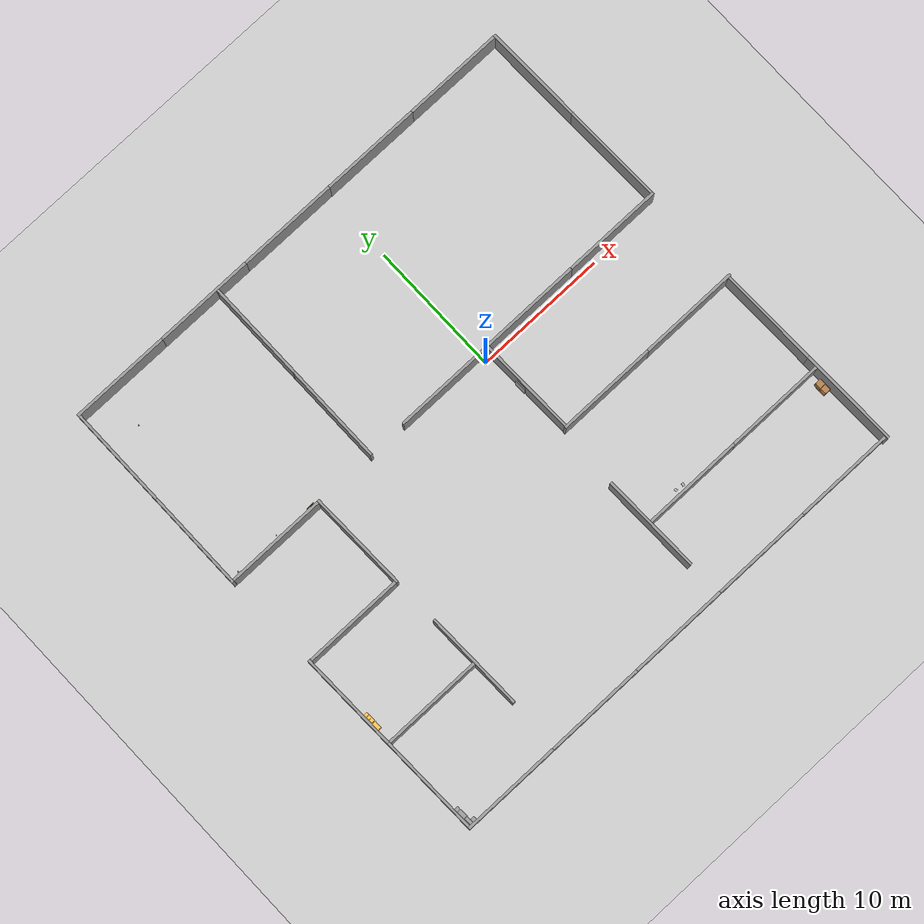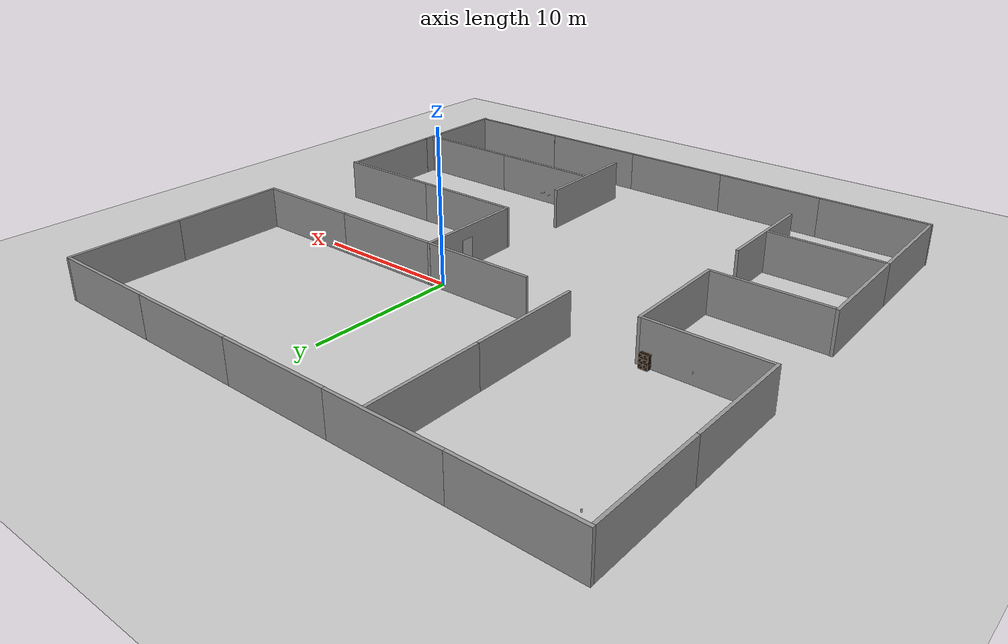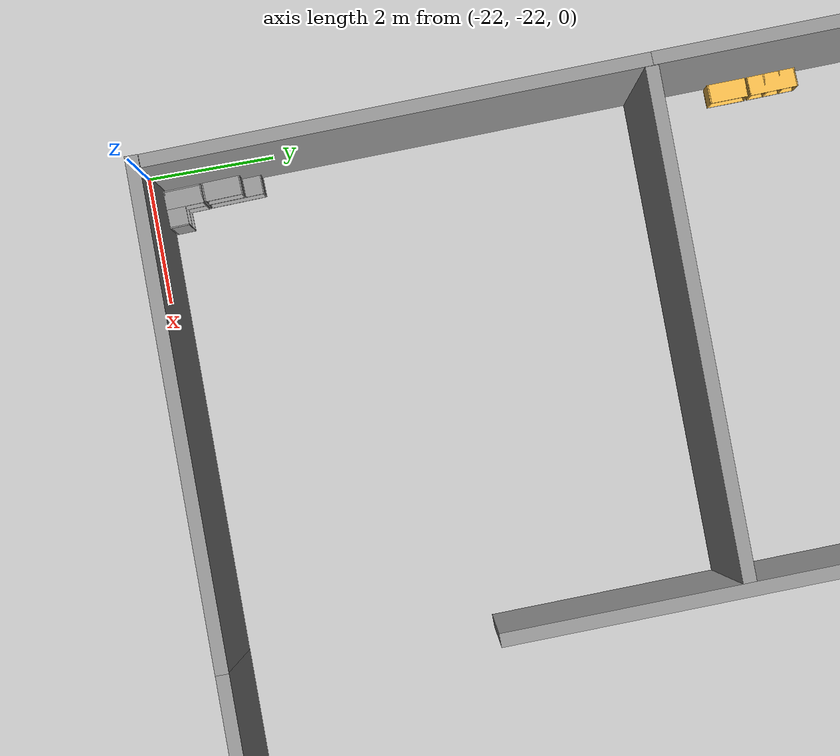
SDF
<sdf version="1.7">
 <world name="default">
  <light name="sun" type="directional">
   <pose>0 0 10 0 -0 0</pose>
   <diffuse>0.8 0.8 0.8 1</diffuse>
   <specular>0.2 0.2 0.2 1</specular>
   <attenuation>
    <range>1000</range>
    <constant>0.9</constant>
    <linear>0.01</linear>
    <quadratic>0.001</quadratic>
   </attenuation>
   <direction>-0.5 0.1 -0.9</direction>
   <spot><inner_angle>0</inner_angle><outer_angle>0</outer_angle><falloff>0</falloff></spot>
  </light>
  <model name="ground_plane">
   <static>1</static>
   <link name="link">
    <collision name="collision">
     <geometry><plane><normal>0 0 1</normal><size>100 100</size></plane></geometry>
     <surface><friction><ode><mu>100</mu><mu2>50</mu2></ode></friction></surface>
    </collision>
    <visual name="visual">
     <cast_shadows>0</cast_shadows>
     <geometry><plane><normal>0 0 1</normal><size>100 100</size></plane></geometry>
     <material>
      <script><uri>file://media/materials/scripts/gazebo.material</uri><name>Gazebo/Grey</name></script>
     </material>
    </visual>
   </link>
  </model>
  <gravity>0 0 -9.8</gravity>
  <magnetic_field>6e-06 2.3e-05 -4.2e-05</magnetic_field>
  <atmosphere type="adiabatic"/>
  <physics type="ode">
   <max_step_size>0.001</max_step_size>
   <real_time_factor>1</real_time_factor>
   <real_time_update_rate>1000</real_time_update_rate>
  </physics>
  <scene><ambient>0.4 0.4 0.4 1</ambient><background>0.7 0.7 0.7 1</background><shadows>1</shadows></scene>
  <spherical_coordinates>
   <surface_model>EARTH_WGS84</surface_model>
   <latitude_deg>0</latitude_deg>
   <longitude_deg>0</longitude_deg>
   <elevation>0</elevation>
   <heading_deg>0</heading_deg>
  </spherical_coordinates>
  <light name="user_directional_light_1" type="directional">
   <pose>-11.4461 8.1371 1 0 -0 0</pose>
   <diffuse>0.5 0.5 0.5 1</diffuse>
   <specular>0.1 0.1 0.1 1</specular>
   <direction>0.1 0.1 -0.9</direction>
   <attenuation>
    <range>20</range>
    <constant>0.5</constant>
    <linear>0.01</linear>
    <quadratic>0.001</quadratic>
   </attenuation>
   <spot><inner_angle>0</inner_angle><outer_angle>0</outer_angle><falloff>0</falloff></spot>
  </light>
  <light name="user_directional_light_2" type="directional">
   <pose>13.1165 9.05579 1 0 -0 0</pose>
   <diffuse>0.5 0.5 0.5 1</diffuse>
   <specular>0.1 0.1 0.1 1</specular>
   <direction>0.1 0.1 -0.9</direction>
   <attenuation>
    <range>20</range>
    <constant>0.5</constant>
    <linear>0.01</linear>
    <quadratic>0.001</quadratic>
   </attenuation>
   <spot><inner_angle>0</inner_angle><outer_angle>0</outer_angle><falloff>0</falloff></spot>
  </light>
  <light name="user_directional_light_3" type="directional">
   <pose>0.316238 -10.7565 1 0 -0 0</pose>
   <diffuse>0.5 0.5 0.5 1</diffuse>
   <specular>0.1 0.1 0.1 1</specular>
   <direction>0.1 0.1 -0.9</direction>
   <attenuation>
    <range>20</range>
    <constant>0.5</constant>
    <linear>0.01</linear>
    <quadratic>0.001</quadratic>
   </attenuation>
   <spot><inner_angle>0</inner_angle><outer_angle>0</outer_angle><falloff>0</falloff></spot>
  </light>
  <light name="user_directional_light_4" type="directional">
   <pose>-1.99105 17.873 1 0 -0 0</pose>
   <diffuse>0.5 0.5 0.5 1</diffuse>
   <specular>0.1 0.1 0.1 1</specular>
   <direction>0.1 0.1 -0.9</direction>
   <attenuation>
    <range>20</range>
    <constant>0.5</constant>
    <linear>0.01</linear>
    <quadratic>0.001</quadratic>
   </attenuation>
   <spot><inner_angle>0</inner_angle><outer_angle>0</outer_angle><falloff>0</falloff></spot>
  </light>
  <model name="grey_wall_clone_4_clone">
   <static>1</static>
   <link name="link">
    <pose>0 0 1.4 0 -0 0</pose>
    <collision name="collision"><geometry><box><size>7.5 0.2 2.8</size></box></geometry></collision>
    <visual name="visual">
     <cast_shadows>0</cast_shadows>
     <geometry><box><size>7.5 0.2 2.8</size></box></geometry>
     <material>
      <script>
       <uri>model://grey_wall/materials/scripts</uri>
       <uri>model://grey_wall/materials/textures</uri>
       <name>vrc/grey_wall</name>
      </script>
     </material>
    </visual>
   </link>
   <pose>15.5082 4.30822 0 0 0 -1.5521</pose>
  </model>
  <model name="grey_wall_clone_4_clone_0">
   <static>1</static>
   <link name="link">
    <pose>0 0 1.4 0 -0 0</pose>
    <collision name="collision"><geometry><box><size>7.5 0.2 2.8</size></box></geometry></collision>
    <visual name="visual">
     <cast_shadows>0</cast_shadows>
     <geometry><box><size>7.5 0.2 2.8</size></box></geometry>
     <material>
      <script>
       <uri>model://grey_wall/materials/scripts</uri>
       <uri>model://grey_wall/materials/textures</uri>
       <name>vrc/grey_wall</name>
      </script>
     </material>
    </visual>
   </link>
   <pose>-14.449 -3.19415 0 0 0 -1.5521</pose>
  </model>
  <light name="user_point_light_0" type="point">
   <pose>26.8068 -65.7611 1 0 -0 0</pose>
   <diffuse>0.5 0.5 0.5 1</diffuse>
   <specular>0.1 0.1 0.1 1</specular>
   <attenuation>
    <range>20</range>
    <constant>0.5</constant>
    <linear>0.01</linear>
    <quadratic>0.001</quadratic>
   </attenuation>
   <cast_shadows>0</cast_shadows>
   <direction>0 0 -1</direction>
   <spot><inner_angle>0</inner_angle><outer_angle>0</outer_angle><falloff>0</falloff></spot>
  </light>
  <model name="grey_wall_clone_4_clone_0_clone">
   <static>1</static>
   <link name="link">
    <pose>0 0 1.4 0 -0 0</pose>
    <collision name="collision"><geometry><box><size>7.5 0.2 2.8</size></box></geometry></collision>
    <visual name="visual">
     <cast_shadows>0</cast_shadows>
     <geometry><box><size>7.5 0.2 2.8</size></box></geometry>
     <material>
      <script>
       <uri>model://grey_wall/materials/scripts</uri>
       <uri>model://grey_wall/materials/textures</uri>
       <name>vrc/grey_wall</name>
      </script>
     </material>
    </visual>
   </link>
   <pose>-22.2112 4.09927 0 0 0 -1.57292</pose>
  </model>
  <audio><device>default</device></audio>
  <model name="grey_wall_clone_4_clone_0_clone_0">
   <static>1</static>
   <link name="link">
    <pose>0 0 1.4 0 -0 0</pose>
    <collision name="collision"><geometry><box><size>7.5 0.2 2.8</size></box></geometry></collision>
    <visual name="visual">
     <cast_shadows>0</cast_shadows>
     <geometry><box><size>7.5 0.2 2.8</size></box></geometry>
     <material>
      <script>
       <uri>model://grey_wall/materials/scripts</uri>
       <uri>model://grey_wall/materials/textures</uri>
       <name>vrc/grey_wall</name>
      </script>
     </material>
    </visual>
   </link>
   <pose>0.647385 -3.19007 0 0 0 -1.5521</pose>
  </model>
  <model name="grey_wall_clone_0">
   <static>1</static>
   <link name="link">
    <pose>0 0 1.4 0 -0 0</pose>
    <collision name="collision"><geometry><box><size>7.5 0.2 2.8</size></box></geometry></collision>
    <visual name="visual">
     <cast_shadows>0</cast_shadows>
     <geometry><box><size>7.5 0.2 2.8</size></box></geometry>
     <material>
      <script>
       <uri>model://grey_wall/materials/scripts</uri>
       <uri>model://grey_wall/materials/textures</uri>
       <name>vrc/grey_wall</name>
      </script>
     </material>
    </visual>
   </link>
   <pose>4.42551 0.460567 0 0 -0 0</pose>
  </model>
  <model name="grey_wall_clone_clone_0_clone">
   <static>1</static>
   <link name="link">
    <pose>0 0 1.4 0 -0 0</pose>
    <collision name="collision"><geometry><box><size>7.5 0.2 2.8</size></box></geometry></collision>
    <visual name="visual">
     <cast_shadows>0</cast_shadows>
     <geometry><box><size>7.5 0.2 2.8</size></box></geometry>
     <material>
      <script>
       <uri>model://grey_wall/materials/scripts</uri>
       <uri>model://grey_wall/materials/textures</uri>
       <name>vrc/grey_wall</name>
      </script>
     </material>
    </visual>
   </link>
   <pose>-18.3631 0.451252 0 0 -0 0</pose>
  </model>
  <model name="grey_wall_clone_clone_0_clone_0">
   <static>1</static>
   <link name="link">
    <pose>0 0 1.4 0 -0 0</pose>
    <collision name="collision"><geometry><box><size>7.5 0.2 2.8</size></box></geometry></collision>
    <visual name="visual">
     <cast_shadows>0</cast_shadows>
     <geometry><box><size>7.5 0.2 2.8</size></box></geometry>
     <material>
      <script>
       <uri>model://grey_wall/materials/scripts</uri>
       <uri>model://grey_wall/materials/textures</uri>
       <name>vrc/grey_wall</name>
      </script>
     </material>
    </visual>
   </link>
   <pose>11.9263 0.46112 0 0 -0 0</pose>
  </model>
  <model name="grey_wall_clone_clone_0_clone_1">
   <static>1</static>
   <link name="link">
    <pose>0 0 1.4 0 -0 0</pose>
    <collision name="collision"><geometry><box><size>7.5 0.2 2.8</size></box></geometry></collision>
    <visual name="visual">
     <cast_shadows>0</cast_shadows>
     <geometry><box><size>7.5 0.2 2.8</size></box></geometry>
     <material>
      <script>
       <uri>model://grey_wall/materials/scripts</uri>
       <uri>model://grey_wall/materials/textures</uri>
       <name>vrc/grey_wall</name>
      </script>
     </material>
    </visual>
   </link>
   <pose>-18.215 -6.85848 0 0 -0 0</pose>
  </model>
  <model name="grey_wall_clone_clone_0_clone_0_clone">
   <static>1</static>
   <link name="link">
    <pose>0 0 1.4 0 -0 0</pose>
    <collision name="collision"><geometry><box><size>7.5 0.2 2.8</size></box></geometry></collision>
    <visual name="visual">
     <cast_shadows>0</cast_shadows>
     <geometry><box><size>7.5 0.2 2.8</size></box></geometry>
     <material>
      <script>
       <uri>model://grey_wall/materials/scripts</uri>
       <uri>model://grey_wall/materials/textures</uri>
       <name>vrc/grey_wall</name>
      </script>
     </material>
    </visual>
   </link>
   <pose>4.35977 -7.00596 0 0 -0 0</pose>
  </model>
  <model name="grey_wall_clone_clone_0_clone_0_clone_0">
   <static>1</static>
   <link name="link">
    <pose>0 0 1.4 0 -0 0</pose>
    <collision name="collision"><geometry><box><size>7.5 0.2 2.8</size></box></geometry></collision>
    <visual name="visual">
     <cast_shadows>0</cast_shadows>
     <geometry><box><size>7.5 0.2 2.8</size></box></geometry>
     <material>
      <script>
       <uri>model://grey_wall/materials/scripts</uri>
       <uri>model://grey_wall/materials/textures</uri>
       <name>vrc/grey_wall</name>
      </script>
     </material>
    </visual>
   </link>
   <pose>11.8582 -7.00493 0 0 -0 0</pose>
  </model>
  <model name="grey_wall_clone_4_clone_0_clone_clone">
   <static>1</static>
   <link name="link">
    <pose>0 0 1.4 0 -0 0</pose>
    <collision name="collision"><geometry><box><size>7.5 0.2 2.8</size></box></geometry></collision>
    <visual name="visual">
     <cast_shadows>0</cast_shadows>
     <geometry><box><size>7.5 0.2 2.8</size></box></geometry>
     <material>
      <script>
       <uri>model://grey_wall/materials/scripts</uri>
       <uri>model://grey_wall/materials/textures</uri>
       <name>vrc/grey_wall</name>
      </script>
     </material>
    </visual>
   </link>
   <pose>-22.1949 11.5941 0 0 0 -1.57292</pose>
  </model>
  <model name="grey_wall_clone_clone_0_clone_2">
   <static>1</static>
   <link name="link">
    <pose>0 0 1.4 0 -0 0</pose>
    <collision name="collision"><geometry><box><size>7.5 0.2 2.8</size></box></geometry></collision>
    <visual name="visual">
     <cast_shadows>0</cast_shadows>
     <geometry><box><size>7.5 0.2 2.8</size></box></geometry>
     <material>
      <script>
       <uri>model://grey_wall/materials/scripts</uri>
       <uri>model://grey_wall/materials/textures</uri>
       <name>vrc/grey_wall</name>
      </script>
     </material>
    </visual>
   </link>
   <pose>-18.5394 15.4379 0 0 -0 0</pose>
  </model>
  <model name="grey_wall_clone_clone_0_clone_3">
   <static>1</static>
   <link name="link">
    <pose>0 0 1.4 0 -0 0</pose>
    <collision name="collision"><geometry><box><size>7.5 0.2 2.8</size></box></geometry></collision>
    <visual name="visual">
     <cast_shadows>0</cast_shadows>
     <geometry><box><size>7.5 0.2 2.8</size></box></geometry>
     <material>
      <script>
       <uri>model://grey_wall/materials/scripts</uri>
       <uri>model://grey_wall/materials/textures</uri>
       <name>vrc/grey_wall</name>
      </script>
     </material>
    </visual>
   </link>
   <pose>-11.0493 15.4397 0 0 -0 0</pose>
  </model>
  <model name="grey_wall_clone_clone_0_clone_4">
   <static>1</static>
   <link name="link">
    <pose>0 0 1.4 0 -0 0</pose>
    <collision name="collision"><geometry><box><size>7.5 0.2 2.8</size></box></geometry></collision>
    <visual name="visual">
     <cast_shadows>0</cast_shadows>
     <geometry><box><size>7.5 0.2 2.8</size></box></geometry>
     <material>
      <script>
       <uri>model://grey_wall/materials/scripts</uri>
       <uri>model://grey_wall/materials/textures</uri>
       <name>vrc/grey_wall</name>
      </script>
     </material>
    </visual>
   </link>
   <pose>-3.54868 15.4378 0 0 -0 0</pose>
  </model>
  <model name="grey_wall_clone_clone_0_clone_5">
   <static>1</static>
   <link name="link">
    <pose>0 0 1.4 0 -0 0</pose>
    <collision name="collision"><geometry><box><size>7.5 0.2 2.8</size></box></geometry></collision>
    <visual name="visual">
     <cast_shadows>0</cast_shadows>
     <geometry><box><size>7.5 0.2 2.8</size></box></geometry>
     <material>
      <script>
       <uri>model://grey_wall/materials/scripts</uri>
       <uri>model://grey_wall/materials/textures</uri>
       <name>vrc/grey_wall</name>
      </script>
     </material>
    </visual>
   </link>
   <pose>3.95078 15.4377 0 0 -0 0</pose>
  </model>
  <model name="grey_wall_clone_clone_0_clone_6">
   <static>1</static>
   <link name="link">
    <pose>0 0 1.4 0 -0 0</pose>
    <collision name="collision"><geometry><box><size>7.5 0.2 2.8</size></box></geometry></collision>
    <visual name="visual">
     <cast_shadows>0</cast_shadows>
     <geometry><box><size>7.5 0.2 2.8</size></box></geometry>
     <material>
      <script>
       <uri>model://grey_wall/materials/scripts</uri>
       <uri>model://grey_wall/materials/textures</uri>
       <name>vrc/grey_wall</name>
      </script>
     </material>
    </visual>
   </link>
   <pose>11.452 15.4377 0 0 -0 0</pose>
  </model>
  <model name="grey_wall_clone_4_clone_clone">
   <static>1</static>
   <link name="link">
    <pose>0 0 1.4 0 -0 0</pose>
    <collision name="collision"><geometry><box><size>7.5 0.2 2.8</size></box></geometry></collision>
    <visual name="visual">
     <cast_shadows>0</cast_shadows>
     <geometry><box><size>7.5 0.2 2.8</size></box></geometry>
     <material>
      <script>
       <uri>model://grey_wall/materials/scripts</uri>
       <uri>model://grey_wall/materials/textures</uri>
       <name>vrc/grey_wall</name>
      </script>
     </material>
    </visual>
   </link>
   <pose>15.3664 11.7883 0 0 0 -1.5521</pose>
  </model>
  <model name="grey_wall_clone_4_clone_0_clone_1">
   <static>1</static>
   <link name="link">
    <pose>0 0 1.4 0 -0 0</pose>
    <collision name="collision"><geometry><box><size>7.5 0.2 2.8</size></box></geometry></collision>
    <visual name="visual">
     <cast_shadows>0</cast_shadows>
     <geometry><box><size>7.5 0.2 2.8</size></box></geometry>
     <material>
      <script>
       <uri>model://grey_wall/materials/scripts</uri>
       <uri>model://grey_wall/materials/textures</uri>
       <name>vrc/grey_wall</name>
      </script>
     </material>
    </visual>
   </link>
   <pose>-21.9989 -10.4818 0 0 0 -1.5521</pose>
  </model>
  <model name="grey_wall_clone_4_clone_0_clone_2">
   <static>1</static>
   <link name="link">
    <pose>0 0 1.4 0 -0 0</pose>
    <collision name="collision"><geometry><box><size>7.5 0.2 2.8</size></box></geometry></collision>
    <visual name="visual">
     <cast_shadows>0</cast_shadows>
     <geometry><box><size>7.5 0.2 2.8</size></box></geometry>
     <material>
      <script>
       <uri>model://grey_wall/materials/scripts</uri>
       <uri>model://grey_wall/materials/textures</uri>
       <name>vrc/grey_wall</name>
      </script>
     </material>
    </visual>
   </link>
   <pose>-21.8568 -17.9712 0 0 0 -1.5521</pose>
  </model>
  <model name="grey_wall_clone_4_clone_0_clone_0_clone">
   <static>1</static>
   <link name="link">
    <pose>0 0 1.4 0 -0 0</pose>
    <collision name="collision"><geometry><box><size>7.5 0.2 2.8</size></box></geometry></collision>
    <visual name="visual">
     <cast_shadows>0</cast_shadows>
     <geometry><box><size>7.5 0.2 2.8</size></box></geometry>
     <material>
      <script>
       <uri>model://grey_wall/materials/scripts</uri>
       <uri>model://grey_wall/materials/textures</uri>
       <name>vrc/grey_wall</name>
      </script>
     </material>
    </visual>
   </link>
   <pose>15.4873 -10.8414 0 0 0 -1.5521</pose>
  </model>
  <model name="grey_wall_clone_4_clone_0_clone_0_clone_0">
   <static>1</static>
   <link name="link">
    <pose>0 0 1.4 0 -0 0</pose>
    <collision name="collision"><geometry><box><size>7.5 0.2 2.8</size></box></geometry></collision>
    <visual name="visual">
     <cast_shadows>0</cast_shadows>
     <geometry><box><size>7.5 0.2 2.8</size></box></geometry>
     <material>
      <script>
       <uri>model://grey_wall/materials/scripts</uri>
       <uri>model://grey_wall/materials/textures</uri>
       <name>vrc/grey_wall</name>
      </script>
     </material>
    </visual>
   </link>
   <pose>15.6252 -18.2818 0 0 0 -1.5521</pose>
  </model>
  <model name="grey_wall_clone_clone_0_clone_0_clone_clone">
   <static>1</static>
   <link name="link">
    <pose>0 0 1.4 0 -0 0</pose>
    <collision name="collision"><geometry><box><size>7.5 0.2 2.8</size></box></geometry></collision>
    <visual name="visual">
     <cast_shadows>0</cast_shadows>
     <geometry><box><size>7.5 0.2 2.8</size></box></geometry>
     <material>
      <script>
       <uri>model://grey_wall/materials/scripts</uri>
       <uri>model://grey_wall/materials/textures</uri>
       <name>vrc/grey_wall</name>
      </script>
     </material>
    </visual>
   </link>
   <pose>-18.1396 -21.8252 0 0 -0 0</pose>
  </model>
  <model name="grey_wall_clone_clone_0_clone_0_clone_clone_0">
   <static>1</static>
   <link name="link">
    <pose>0 0 1.4 0 -0 0</pose>
    <collision name="collision"><geometry><box><size>7.5 0.2 2.8</size></box></geometry></collision>
    <visual name="visual">
     <cast_shadows>0</cast_shadows>
     <geometry><box><size>7.5 0.2 2.8</size></box></geometry>
     <material>
      <script>
       <uri>model://grey_wall/materials/scripts</uri>
       <uri>model://grey_wall/materials/textures</uri>
       <name>vrc/grey_wall</name>
      </script>
     </material>
    </visual>
   </link>
   <pose>-10.6534 -21.8234 0 0 -0 0</pose>
  </model>
  <model name="grey_wall_clone_clone_0_clone_0_clone_clone_1">
   <static>1</static>
   <link name="link">
    <pose>0 0 1.4 0 -0 0</pose>
    <collision name="collision"><geometry><box><size>7.5 0.2 2.8</size></box></geometry></collision>
    <visual name="visual">
     <cast_shadows>0</cast_shadows>
     <geometry><box><size>7.5 0.2 2.8</size></box></geometry>
     <material>
      <script>
       <uri>model://grey_wall/materials/scripts</uri>
       <uri>model://grey_wall/materials/textures</uri>
       <name>vrc/grey_wall</name>
      </script>
     </material>
    </visual>
   </link>
   <pose>-3.16614 -21.8218 0 0 -0 0</pose>
  </model>
  <model name="grey_wall_clone_clone_0_clone_0_clone_clone_2">
   <static>1</static>
   <link name="link">
    <pose>0 0 1.4 0 -0 0</pose>
    <collision name="collision"><geometry><box><size>7.5 0.2 2.8</size></box></geometry></collision>
    <visual name="visual">
     <cast_shadows>0</cast_shadows>
     <geometry><box><size>7.5 0.2 2.8</size></box></geometry>
     <material>
      <script>
       <uri>model://grey_wall/materials/scripts</uri>
       <uri>model://grey_wall/materials/textures</uri>
       <name>vrc/grey_wall</name>
      </script>
     </material>
    </visual>
   </link>
   <pose>4.33462 -21.8217 0 0 -0 0</pose>
  </model>
  <model name="grey_wall_clone_clone_0_clone_0_clone_clone_3">
   <static>1</static>
   <link name="link">
    <pose>0 0 1.4 0 -0 0</pose>
    <collision name="collision"><geometry><box><size>7.5 0.2 2.8</size></box></geometry></collision>
    <visual name="visual">
     <cast_shadows>0</cast_shadows>
     <geometry><box><size>7.5 0.2 2.8</size></box></geometry>
     <material>
      <script>
       <uri>model://grey_wall/materials/scripts</uri>
       <uri>model://grey_wall/materials/textures</uri>
       <name>vrc/grey_wall</name>
      </script>
     </material>
    </visual>
   </link>
   <pose>11.8265 -21.8133 0 0 -0 0</pose>
  </model>
  <model name="door">
   <link name="link_0">
    <visual name="visual">
     <pose>0 0 1 0 -0 0</pose>
     <geometry><box><size>0.9 0.15 2</size></box></geometry>
     <material>
      <script>
       <uri>model://door/materials/scripts</uri>
       <uri>model://door/materials/textures</uri>
       <name>door</name>
      </script>
     </material>
    </visual>
    <collision name="collision">
     <pose>0 0 1 0 -0 0</pose>
     <geometry><box><size>0.9 0.15 2</size></box></geometry>
    </collision>
   </link>
   <static>1</static>
   <pose>0.558432 -2.83222 0 0 0 -1.54638</pose>
  </model>
  <model name="cabinet">
   <static>1</static>
   <link name="cabinet_bottom_plate">
    <inertial>
     <pose>0 0 -1 0 -0 0</pose>
     <inertia><ixx>2.05</ixx><ixy>0</ixy><ixz>0</ixz><iyy>2.05</iyy><iyz>0</iyz><izz>2.05</izz></inertia>
     <mass>25</mass>
    </inertial>
    <collision name="cabinet_bottom_plate_geom">
     <pose>0 0 0.01 0 -0 0</pose>
     <geometry><box><size>0.45 0.45 0.02</size></box></geometry>
    </collision>
    <visual name="cabinet_bottom_plate_geom_visual">
     <pose>0 0 0.01 0 -0 0</pose>
     <geometry><box><size>0.45 0.45 0.02</size></box></geometry>
     <material>
      <script><uri>file://media/materials/scripts/gazebo.material</uri><name>Gazebo/Wood</name></script>
     </material>
    </visual>
    <collision name="cabinet_bottom_plate_geom_cabinet_back_plate">
     <pose>0.235 0 0.51 0 -0 0</pose>
     <geometry><box><size>0.02 0.45 1.02</size></box></geometry>
    </collision>
    <visual name="cabinet_bottom_plate_geom_cabinet_back_plate_visual">
     <pose>0.235 0 0.51 0 -0 0</pose>
     <geometry><box><size>0.02 0.45 1.02</size></box></geometry>
     <material>
      <script><uri>file://media/materials/scripts/gazebo.material</uri><name>Gazebo/Wood</name></script>
     </material>
    </visual>
    <collision name="cabinet_bottom_plate_geom_cabinet_left_plate">
     <pose>0 0.235 0.51 0 -0 0</pose>
     <geometry><box><size>0.45 0.02 1.02</size></box></geometry>
    </collision>
    <visual name="cabinet_bottom_plate_geom_cabinet_left_plate_visual">
     <pose>0 0.235 0.51 0 -0 0</pose>
     <geometry><box><size>0.45 0.02 1.02</size></box></geometry>
     <material>
      <script><uri>file://media/materials/scripts/gazebo.material</uri><name>Gazebo/Wood</name></script>
     </material>
    </visual>
    <collision name="cabinet_bottom_plate_geom_cabinet_middle_plate">
     <pose>0 0 0.51 0 -0 0</pose>
     <geometry><box><size>0.45 0.45 0.02</size></box></geometry>
    </collision>
    <visual name="cabinet_bottom_plate_geom_cabinet_middle_plate_visual">
     <pose>0 0 0.51 0 -0 0</pose>
     <geometry><box><size>0.45 0.45 0.02</size></box></geometry>
     <material>
      <script><uri>file://media/materials/scripts/gazebo.material</uri><name>Gazebo/Wood</name></script>
     </material>
    </visual>
    <collision name="cabinet_bottom_plate_geom_cabinet_right_plate">
     <pose>0 -0.235 0.51 0 -0 0</pose>
     <geometry><box><size>0.45 0.02 1.02</size></box></geometry>
    </collision>
    <visual name="cabinet_bottom_plate_geom_cabinet_right_plate_visual">
     <pose>0 -0.235 0.51 0 -0 0</pose>
     <geometry><box><size>0.45 0.02 1.02</size></box></geometry>
     <material>
      <script><uri>file://media/materials/scripts/gazebo.material</uri><name>Gazebo/Wood</name></script>
     </material>
    </visual>
    <collision name="cabinet_bottom_plate_geom_cabinet_top_plate">
     <pose>0 0 1.01 0 -0 0</pose>
     <geometry><box><size>0.45 0.45 0.02</size></box></geometry>
    </collision>
    <visual name="cabinet_bottom_plate_geom_cabinet_top_plate_visual">
     <pose>0 0 1.01 0 -0 0</pose>
     <geometry><box><size>0.45 0.45 0.02</size></box></geometry>
     <material>
      <script><uri>file://media/materials/scripts/gazebo.material</uri><name>Gazebo/Wood</name></script>
     </material>
    </visual>
   </link>
   <pose>15.2039 -16.2791 0 0 -0 0</pose>
  </model>
  <model name="cabinet_clone">
   <static>1</static>
   <link name="cabinet_bottom_plate">
    <inertial>
     <pose>0 0 -1 0 -0 0</pose>
     <inertia><ixx>2.05</ixx><ixy>0</ixy><ixz>0</ixz><iyy>2.05</iyy><iyz>0</iyz><izz>2.05</izz></inertia>
     <mass>25</mass>
    </inertial>
    <collision name="cabinet_bottom_plate_geom">
     <pose>0 0 0.01 0 -0 0</pose>
     <geometry><box><size>0.45 0.45 0.02</size></box></geometry>
    </collision>
    <visual name="cabinet_bottom_plate_geom_visual">
     <pose>0 0 0.01 0 -0 0</pose>
     <geometry><box><size>0.45 0.45 0.02</size></box></geometry>
     <material>
      <script><uri>file://media/materials/scripts/gazebo.material</uri><name>Gazebo/Wood</name></script>
     </material>
    </visual>
    <collision name="cabinet_bottom_plate_geom_cabinet_back_plate">
     <pose>0.235 0 0.51 0 -0 0</pose>
     <geometry><box><size>0.02 0.45 1.02</size></box></geometry>
    </collision>
    <visual name="cabinet_bottom_plate_geom_cabinet_back_plate_visual">
     <pose>0.235 0 0.51 0 -0 0</pose>
     <geometry><box><size>0.02 0.45 1.02</size></box></geometry>
     <material>
      <script><uri>file://media/materials/scripts/gazebo.material</uri><name>Gazebo/Wood</name></script>
     </material>
    </visual>
    <collision name="cabinet_bottom_plate_geom_cabinet_left_plate">
     <pose>0 0.235 0.51 0 -0 0</pose>
     <geometry><box><size>0.45 0.02 1.02</size></box></geometry>
    </collision>
    <visual name="cabinet_bottom_plate_geom_cabinet_left_plate_visual">
     <pose>0 0.235 0.51 0 -0 0</pose>
     <geometry><box><size>0.45 0.02 1.02</size></box></geometry>
     <material>
      <script><uri>file://media/materials/scripts/gazebo.material</uri><name>Gazebo/Wood</name></script>
     </material>
    </visual>
    <collision name="cabinet_bottom_plate_geom_cabinet_middle_plate">
     <pose>0 0 0.51 0 -0 0</pose>
     <geometry><box><size>0.45 0.45 0.02</size></box></geometry>
    </collision>
    <visual name="cabinet_bottom_plate_geom_cabinet_middle_plate_visual">
     <pose>0 0 0.51 0 -0 0</pose>
     <geometry><box><size>0.45 0.45 0.02</size></box></geometry>
     <material>
      <script><uri>file://media/materials/scripts/gazebo.material</uri><name>Gazebo/Wood</name></script>
     </material>
    </visual>
    <collision name="cabinet_bottom_plate_geom_cabinet_right_plate">
     <pose>0 -0.235 0.51 0 -0 0</pose>
     <geometry><box><size>0.45 0.02 1.02</size></box></geometry>
    </collision>
    <visual name="cabinet_bottom_plate_geom_cabinet_right_plate_visual">
     <pose>0 -0.235 0.51 0 -0 0</pose>
     <geometry><box><size>0.45 0.02 1.02</size></box></geometry>
     <material>
      <script><uri>file://media/materials/scripts/gazebo.material</uri><name>Gazebo/Wood</name></script>
     </material>
    </visual>
    <collision name="cabinet_bottom_plate_geom_cabinet_top_plate">
     <pose>0 0 1.01 0 -0 0</pose>
     <geometry><box><size>0.45 0.45 0.02</size></box></geometry>
    </collision>
    <visual name="cabinet_bottom_plate_geom_cabinet_top_plate_visual">
     <pose>0 0 1.01 0 -0 0</pose>
     <geometry><box><size>0.45 0.45 0.02</size></box></geometry>
     <material>
      <script><uri>file://media/materials/scripts/gazebo.material</uri><name>Gazebo/Wood</name></script>
     </material>
    </visual>
   </link>
   <pose>15.1941 -16.7787 0 0 -0 0</pose>
  </model>
  <model name="book_1">
   <link name="cover">
    <pose>0 -0.000108 0.015405 0 -0 0</pose>
    <visual name="visual">
     <geometry><box><size>0.245 0.16 0.03</size></box></geometry>
     <material>
      <script>
       <uri>model://book_1/materials/scripts</uri>
       <uri>model://book_1/materials/textures</uri>
       <name>book_1</name>
      </script>
     </material>
    </visual>
    <collision name="collision"><geometry><box><size>0.245 0.16 0.03</size></box></geometry></collision>
   </link>
   <link name="page">
    <pose>0 0.000608 0.015405 0 -0 0</pose>
    <visual name="visual">
     <geometry><box><size>0.24502 0.15862 0.028</size></box></geometry>
     <material>
      <lighting>1</lighting>
      <ambient>1 1 1 1</ambient>
      <diffuse>1 1 1 1</diffuse>
      <specular>0.01 0.01 0.01 1</specular>
      <emissive>0 0 0 1</emissive>
      <shader type="vertex"><normal_map>__default__</normal_map></shader>
     </material>
    </visual>
    <collision name="collision"><geometry><box><size>0.245 0.16 0.03</size></box></geometry></collision>
   </link>
   <static>1</static>
   <pose>3.3312 -14.8779 0.800647 0 -0 1.93686</pose>
  </model>
  <model name="book_10">
   <link name="cover">
    <pose>0 -0.000108 0.015405 0 -0 0</pose>
    <visual name="visual">
     <geometry><box><size>0.245 0.16 0.03</size></box></geometry>
     <material>
      <script>
       <uri>model://book_10/materials/scripts</uri>
       <uri>model://book_10/materials/textures</uri>
       <name>book_10</name>
      </script>
     </material>
    </visual>
    <collision name="collision"><geometry><box><size>0.245 0.16 0.03</size></box></geometry></collision>
   </link>
   <link name="page">
    <pose>0 0.000608 0.015405 0 -0 0</pose>
    <visual name="visual">
     <geometry><box><size>0.24502 0.15862 0.028</size></box></geometry>
     <material>
      <lighting>1</lighting>
      <ambient>1 1 1 1</ambient>
      <diffuse>1 1 1 1</diffuse>
      <specular>0.01 0.01 0.01 1</specular>
      <emissive>0 0 0 1</emissive>
      <shader type="vertex"><normal_map>__default__</normal_map></shader>
     </material>
    </visual>
    <collision name="collision"><geometry><box><size>0.245 0.16 0.03</size></box></geometry></collision>
   </link>
   <static>1</static>
   <pose>3.91921 -14.9443 0.826943 0 0 -1.74766</pose>
  </model>
  <model name="grey_wall_clone_clone_0_clone_1_clone">
   <static>1</static>
   <link name="link">
    <pose>0 0 1.4 0 -0 0</pose>
    <collision name="collision"><geometry><box><size>7.5 0.2 2.8</size></box></geometry></collision>
    <visual name="visual">
     <cast_shadows>0</cast_shadows>
     <geometry><box><size>7.5 0.2 2.8</size></box></geometry>
     <material>
      <script>
       <uri>model://grey_wall/materials/scripts</uri>
       <uri>model://grey_wall/materials/textures</uri>
       <name>vrc/grey_wall</name>
      </script>
     </material>
    </visual>
   </link>
   <pose>-18.0733 -14.2546 0 0 -0 0</pose>
  </model>
  <model name="grey_wall_clone_4_clone_0_clone_3">
   <static>1</static>
   <link name="link">
    <pose>0 0 1.4 0 -0 0</pose>
    <collision name="collision"><geometry><box><size>7.5 0.2 2.8</size></box></geometry></collision>
    <visual name="visual">
     <cast_shadows>0</cast_shadows>
     <geometry><box><size>7.5 0.2 2.8</size></box></geometry>
     <material>
      <script>
       <uri>model://grey_wall/materials/scripts</uri>
       <uri>model://grey_wall/materials/textures</uri>
       <name>vrc/grey_wall</name>
      </script>
     </material>
    </visual>
   </link>
   <pose>-14.2282 -14.1275 0 0 0 -1.5521</pose>
  </model>
  <model name="Wall_Cabinet_Coin_24x30W">
   <link name="Wall_10">
    <pose>0.286 -0.148 0.384 0 -0 0</pose>
    <inertial>
     <mass>2.1259</mass>
     <inertia><ixx>0.0158</ixx><iyy>0.1202</iyy><izz>0.1046</izz><ixy>0</ixy><ixz>0</ixz><iyz>0</iyz></inertia>
    </inertial>
    <collision name="Wall_10_Collision"><geometry><box><size>0.02 0.296 0.768</size></box></geometry></collision>
    <visual name="Wall_10_Visual">
     <geometry><box><size>0.02 0.296 0.768</size></box></geometry>
     <material>
      <script><uri>file://media/materials/scripts/gazebo.material</uri><name>Gazebo/Grey</name></script>
      <ambient>1 1 1 1</ambient>
     </material>
    </visual>
   </link>
   <joint name="10_16" type="fixed">
    <pose>0 0 -0.374 0 -0 0</pose>
    <parent>Wall_16</parent>
    <child>Wall_10</child>
    <axis><xyz>1 0 0</xyz><limit><lower>-1e+16</lower><upper>1e+16</upper></limit></axis>
   </joint>
   <joint name="10_14" type="fixed">
    <parent>Wall_14</parent>
    <child>Wall_10</child>
    <axis><xyz>1 0 0</xyz><limit><lower>-1e+16</lower><upper>1e+16</upper></limit></axis>
   </joint>
   <joint name="10_12" type="fixed">
    <pose>0 0 0.374 0 -0 0</pose>
    <parent>Wall_12</parent>
    <child>Wall_10</child>
    <axis><xyz>1 0 0</xyz><limit><lower>-1e+16</lower><upper>1e+16</upper></limit></axis>
   </joint>
   <joint name="10_29" type="fixed">
    <pose>0 -0.148 0 0 -0 0</pose>
    <parent>Wall_29</parent>
    <child>Wall_10</child>
    <axis><xyz>1 0 0</xyz><limit><lower>-1e+16</lower><upper>1e+16</upper></limit></axis>
   </joint>
   <link name="Wall_12">
    <pose>0.148 -0.148 0.758 0 -0 0</pose>
    <inertial>
     <mass>0.8802</mass>
     <inertia><ixx>0.0065</ixx><iyy>0.0139</iyy><izz>0.0074</izz><ixy>0</ixy><ixz>0</ixz><iyz>0</iyz></inertia>
    </inertial>
    <collision name="Wall_12_Collision"><geometry><box><size>0.296 0.296 0.02</size></box></geometry></collision>
    <visual name="Wall_12_Visual">
     <geometry><box><size>0.296 0.296 0.02</size></box></geometry>
     <material>
      <script><uri>file://media/materials/scripts/gazebo.material</uri><name>Gazebo/Grey</name></script>
      <ambient>1 1 1 1</ambient>
     </material>
    </visual>
   </link>
   <joint name="12_29" type="fixed">
    <pose>0 -0.148 0 0 -0 0</pose>
    <parent>Wall_29</parent>
    <child>Wall_12</child>
    <axis><xyz>0 0 1</xyz><limit><lower>-1e+16</lower><upper>1e+16</upper></limit></axis>
   </joint>
   <link name="Wall_14">
    <pose>0.148 -0.148 0.384 0 -0 0</pose>
    <inertial>
     <mass>0.8802</mass>
     <inertia><ixx>0.0065</ixx><iyy>0.0139</iyy><izz>0.0074</izz><ixy>0</ixy><ixz>0</ixz><iyz>0</iyz></inertia>
    </inertial>
    <collision name="Wall_14_Collision"><geometry><box><size>0.296 0.296 0.02</size></box></geometry></collision>
    <visual name="Wall_14_Visual">
     <geometry><box><size>0.296 0.296 0.02</size></box></geometry>
     <material>
      <script><uri>file://media/materials/scripts/gazebo.material</uri><name>Gazebo/Grey</name></script>
      <ambient>1 1 1 1</ambient>
     </material>
    </visual>
   </link>
   <joint name="14_29" type="fixed">
    <pose>0 -0.148 0 0 -0 0</pose>
    <parent>Wall_29</parent>
    <child>Wall_14</child>
    <axis><xyz>0 1 0</xyz><limit><lower>-1e+16</lower><upper>1e+16</upper></limit></axis>
   </joint>
   <link name="Wall_16">
    <pose>0.148 -0.148 0.01 0 -0 0</pose>
    <inertial>
     <mass>0.8802</mass>
     <inertia><ixx>0.0065</ixx><iyy>0.0139</iyy><izz>0.0074</izz><ixy>0</ixy><ixz>0</ixz><iyz>0</iyz></inertia>
    </inertial>
    <collision name="Wall_16_Collision"><geometry><box><size>0.296 0.296 0.02</size></box></geometry></collision>
    <visual name="Wall_16_Visual">
     <geometry><box><size>0.296 0.296 0.02</size></box></geometry>
     <material>
      <script><uri>file://media/materials/scripts/gazebo.material</uri><name>Gazebo/Grey</name></script>
      <ambient>1 1 1 1</ambient>
     </material>
    </visual>
   </link>
   <joint name="16_29" type="fixed">
    <pose>0 -0.148 0 0 -0 0</pose>
    <parent>Wall_29</parent>
    <child>Wall_16</child>
    <axis><xyz>0 1 0</xyz><limit><lower>-1e+16</lower><upper>1e+16</upper></limit></axis>
   </joint>
   <link name="Wall_18">
    <pose>-0.148 0 0.01 0 -0 0</pose>
    <inertial>
     <mass>1.6525</mass>
     <inertia><ixx>0.0491</ixx><iyy>0.0613</iyy><izz>0.0123</izz><ixy>0</ixy><ixz>0</ixz><iyz>0</iyz></inertia>
    </inertial>
    <collision name="Wall_18_Collision"><geometry><box><size>0.296 0.592 0.02</size></box></geometry></collision>
    <visual name="Wall_18_Visual">
     <geometry><box><size>0.296 0.592 0.02</size></box></geometry>
     <material>
      <script><uri>file://media/materials/scripts/gazebo.material</uri><name>Gazebo/Grey</name></script>
      <ambient>1 1 1 1</ambient>
     </material>
    </visual>
   </link>
   <joint name="18_16" type="fixed">
    <pose>0.148 -0.148 0 0 -0 0</pose>
    <parent>Wall_16</parent>
    <child>Wall_18</child>
    <axis><xyz>1 0 0</xyz><limit><lower>-1e+16</lower><upper>1e+16</upper></limit></axis>
   </joint>
   <joint name="18_29" type="fixed">
    <pose>0 -0.296 0 0 -0 0</pose>
    <parent>Wall_29</parent>
    <child>Wall_18</child>
    <axis><xyz>0 1 0</xyz><limit><lower>-1e+16</lower><upper>1e+16</upper></limit></axis>
   </joint>
   <joint name="18_27" type="fixed">
    <pose>-0.148 0 0 0 -0 0</pose>
    <parent>Wall_27</parent>
    <child>Wall_18</child>
    <axis><xyz>1 0 0</xyz><limit><lower>-1e+16</lower><upper>1e+16</upper></limit></axis>
   </joint>
   <joint name="18_30" type="fixed">
    <pose>0 0.296 0 0 -0 0</pose>
    <parent>Wall_30</parent>
    <child>Wall_18</child>
    <axis><xyz>0 1 0</xyz><limit><lower>-1e+16</lower><upper>1e+16</upper></limit></axis>
   </joint>
   <link name="Wall_20">
    <pose>-0.148 0 0.384 0 -0 0</pose>
    <inertial>
     <mass>1.6525</mass>
     <inertia><ixx>0.0491</ixx><iyy>0.0613</iyy><izz>0.0123</izz><ixy>0</ixy><ixz>0</ixz><iyz>0</iyz></inertia>
    </inertial>
    <collision name="Wall_20_Collision"><geometry><box><size>0.296 0.592 0.02</size></box></geometry></collision>
    <visual name="Wall_20_Visual">
     <geometry><box><size>0.296 0.592 0.02</size></box></geometry>
     <material>
      <script><uri>file://media/materials/scripts/gazebo.material</uri><name>Gazebo/Grey</name></script>
      <ambient>1 1 1 1</ambient>
     </material>
    </visual>
   </link>
   <joint name="20_14" type="fixed">
    <pose>0.148 -0.148 0 0 -0 0</pose>
    <parent>Wall_14</parent>
    <child>Wall_20</child>
    <axis><xyz>1 0 0</xyz><limit><lower>-1e+16</lower><upper>1e+16</upper></limit></axis>
   </joint>
   <joint name="20_29" type="fixed">
    <pose>0 -0.296 0 0 -0 0</pose>
    <parent>Wall_29</parent>
    <child>Wall_20</child>
    <axis><xyz>0 1 0</xyz><limit><lower>-1e+16</lower><upper>1e+16</upper></limit></axis>
   </joint>
   <joint name="20_27" type="fixed">
    <pose>-0.148 0 0 0 -0 0</pose>
    <parent>Wall_27</parent>
    <child>Wall_20</child>
    <axis><xyz>1 0 0</xyz><limit><lower>-1e+16</lower><upper>1e+16</upper></limit></axis>
   </joint>
   <joint name="20_30" type="fixed">
    <pose>0 0.296 0 0 -0 0</pose>
    <parent>Wall_30</parent>
    <child>Wall_20</child>
    <axis><xyz>0 1 0</xyz><limit><lower>-1e+16</lower><upper>1e+16</upper></limit></axis>
   </joint>
   <link name="Wall_22">
    <pose>-0.148 0 0.758 0 -0 0</pose>
    <inertial>
     <mass>1.6525</mass>
     <inertia><ixx>0.0491</ixx><iyy>0.0613</iyy><izz>0.0123</izz><ixy>0</ixy><ixz>0</ixz><iyz>0</iyz></inertia>
    </inertial>
    <collision name="Wall_22_Collision"><geometry><box><size>0.296 0.592 0.02</size></box></geometry></collision>
    <visual name="Wall_22_Visual">
     <geometry><box><size>0.296 0.592 0.02</size></box></geometry>
     <material>
      <script><uri>file://media/materials/scripts/gazebo.material</uri><name>Gazebo/Grey</name></script>
      <ambient>1 1 1 1</ambient>
     </material>
    </visual>
   </link>
   <joint name="22_12" type="fixed">
    <pose>0.148 -0.148 0 0 -0 0</pose>
    <parent>Wall_12</parent>
    <child>Wall_22</child>
    <axis><xyz>1 0 0</xyz><limit><lower>-1e+16</lower><upper>1e+16</upper></limit></axis>
   </joint>
   <joint name="22_29" type="fixed">
    <pose>0 -0.296 0 0 -0 0</pose>
    <parent>Wall_29</parent>
    <child>Wall_22</child>
    <axis><xyz>0 1 0</xyz><limit><lower>-1e+16</lower><upper>1e+16</upper></limit></axis>
   </joint>
   <joint name="22_27" type="fixed">
    <pose>-0.148 0 0 0 -0 0</pose>
    <parent>Wall_27</parent>
    <child>Wall_22</child>
    <axis><xyz>1 0 0</xyz><limit><lower>-1e+16</lower><upper>1e+16</upper></limit></axis>
   </joint>
   <joint name="22_30" type="fixed">
    <pose>0 0.296 0 0 -0 0</pose>
    <parent>Wall_30</parent>
    <child>Wall_22</child>
    <axis><xyz>0 1 0</xyz><limit><lower>-1e+16</lower><upper>1e+16</upper></limit></axis>
   </joint>
   <link name="Wall_27">
    <pose>-0.286 0 0.384 0 -0 0</pose>
    <inertial>
     <mass>4.2589</mass>
     <inertia><ixx>0.1266</ixx><iyy>0.3358</iyy><izz>0.2095</izz><ixy>0</ixy><ixz>0</ixz><iyz>0</iyz></inertia>
    </inertial>
    <collision name="Wall_27_Collision"><geometry><box><size>0.02 0.592 0.768</size></box></geometry></collision>
    <visual name="Wall_27_Visual">
     <geometry><box><size>0.02 0.592 0.768</size></box></geometry>
     <material>
      <script><uri>file://media/materials/scripts/gazebo.material</uri><name>Gazebo/Grey</name></script>
      <ambient>1 1 1 1</ambient>
     </material>
    </visual>
   </link>
   <joint name="27_30" type="fixed">
    <pose>0 0.296 0 0 -0 0</pose>
    <parent>Wall_30</parent>
    <child>Wall_27</child>
    <axis><xyz>0 1 0</xyz><limit><lower>-1e+16</lower><upper>1e+16</upper></limit></axis>
   </joint>
   <link name="Wall_29">
    <pose>0 -0.286 0.384 0 -0 0</pose>
    <inertial>
     <mass>4.3176</mass>
     <inertia><ixx>0.134</ixx><iyy>0.2091</iyy><izz>0.3428</izz><ixy>0</ixy><ixz>0</ixz><iyz>0</iyz></inertia>
    </inertial>
    <collision name="Wall_29_Collision"><geometry><box><size>0.592 0.02 0.768</size></box></geometry></collision>
    <visual name="Wall_29_Visual">
     <geometry><box><size>0.592 0.02 0.768</size></box></geometry>
     <material>
      <script><uri>file://media/materials/scripts/gazebo.material</uri><name>Gazebo/Grey</name></script>
      <ambient>1 1 1 1</ambient>
     </material>
    </visual>
   </link>
   <link name="Wall_30">
    <pose>-0.148 0.286 0.384 0 -0 0</pose>
    <inertial>
     <mass>2.1093</mass>
     <inertia><ixx>0.1021</ixx><iyy>0.0157</iyy><izz>0.1177</izz><ixy>0</ixy><ixz>0</ixz><iyz>0</iyz></inertia>
    </inertial>
    <collision name="Wall_30_Collision"><geometry><box><size>0.296 0.02 0.768</size></box></geometry></collision>
    <visual name="Wall_30_Visual">
     <geometry><box><size>0.296 0.02 0.768</size></box></geometry>
     <material>
      <script><uri>file://media/materials/scripts/gazebo.material</uri><name>Gazebo/Grey</name></script>
      <ambient>1 1 1 1</ambient>
     </material>
    </visual>
   </link>
   <static>1</static>
   <pose>-21.362 -21.4193 0 0 -0 0.031344</pose>
  </model>
  <model name="Wall_Cabinet_36x15W">
   <link name="Wall_0">
    <pose>0 0 0.01 0 -0 0</pose>
    <inertial>
     <mass>1.9796</mass>
     <inertia><ixx>0.0145</ixx><iyy>0.1511</iyy><izz>0.1367</izz><ixy>0</ixy><ixz>0</ixz><iyz>0</iyz></inertia>
    </inertial>
    <collision name="Wall_0_Collision"><geometry><box><size>0.91 0.296 0.02</size></box></geometry></collision>
    <visual name="Wall_0_Visual">
     <geometry><box><size>0.91 0.296 0.02</size></box></geometry>
     <material>
      <script><uri>file://media/materials/scripts/gazebo.material</uri><name>Gazebo/Grey</name></script>
      <ambient>1 1 1 1</ambient>
     </material>
    </visual>
   </link>
   <joint name="0_2" type="fixed">
    <pose>-0.455 0 0 0 -0 0</pose>
    <parent>Wall_2</parent>
    <child>Wall_0</child>
    <axis><xyz>0 0 1</xyz><limit><lower>-1e+16</lower><upper>1e+16</upper></limit></axis>
   </joint>
   <joint name="0_4" type="fixed">
    <pose>0.455 0 0 0 -0 0</pose>
    <parent>Wall_4</parent>
    <child>Wall_0</child>
    <axis><xyz>0 0 1</xyz><limit><lower>-1e+16</lower><upper>1e+16</upper></limit></axis>
   </joint>
   <joint name="0_8" type="fixed">
    <pose>0 -0.148 0 0 -0 0</pose>
    <parent>Wall_8</parent>
    <child>Wall_0</child>
    <axis><xyz>0 0 1</xyz><limit><lower>-1e+16</lower><upper>1e+16</upper></limit></axis>
   </joint>
   <link name="Wall_2">
    <pose>-0.445 0 0.192 0 -0 0</pose>
    <inertial>
     <mass>0.8353</mass>
     <inertia><ixx>0.0061</ixx><iyy>0.0164</iyy><izz>0.0103</izz><ixy>0</ixy><ixz>0</ixz><iyz>0</iyz></inertia>
    </inertial>
    <collision name="Wall_2_Collision"><geometry><box><size>0.02 0.296 0.384</size></box></geometry></collision>
    <visual name="Wall_2_Visual">
     <geometry><box><size>0.02 0.296 0.384</size></box></geometry>
     <material>
      <script><uri>file://media/materials/scripts/gazebo.material</uri><name>Gazebo/Grey</name></script>
      <ambient>1 1 1 1</ambient>
     </material>
    </visual>
   </link>
   <link name="Wall_4">
    <pose>0.445 0 0.192 0 -0 0</pose>
    <inertial>
     <mass>0.8353</mass>
     <inertia><ixx>0.0061</ixx><iyy>0.0164</iyy><izz>0.0103</izz><ixy>0</ixy><ixz>0</ixz><iyz>0</iyz></inertia>
    </inertial>
    <collision name="Wall_4_Collision"><geometry><box><size>0.02 0.296 0.384</size></box></geometry></collision>
    <visual name="Wall_4_Visual">
     <geometry><box><size>0.02 0.296 0.384</size></box></geometry>
     <material>
      <script><uri>file://media/materials/scripts/gazebo.material</uri><name>Gazebo/Grey</name></script>
      <ambient>1 1 1 1</ambient>
     </material>
    </visual>
   </link>
   <link name="Wall_6">
    <pose>0 0 0.374 0 -0 0</pose>
    <inertial>
     <mass>1.9796</mass>
     <inertia><ixx>0.0145</ixx><iyy>0.1511</iyy><izz>0.1367</izz><ixy>0</ixy><ixz>0</ixz><iyz>0</iyz></inertia>
    </inertial>
    <collision name="Wall_6_Collision"><geometry><box><size>0.91 0.296 0.02</size></box></geometry></collision>
    <visual name="Wall_6_Visual">
     <geometry><box><size>0.91 0.296 0.02</size></box></geometry>
     <material>
      <script><uri>file://media/materials/scripts/gazebo.material</uri><name>Gazebo/Grey</name></script>
      <ambient>1 1 1 1</ambient>
     </material>
    </visual>
   </link>
   <joint name="6_2" type="fixed">
    <pose>-0.455 0 0 0 -0 0</pose>
    <parent>Wall_2</parent>
    <child>Wall_6</child>
    <axis><xyz>0 0 1</xyz><limit><lower>-1e+16</lower><upper>1e+16</upper></limit></axis>
   </joint>
   <joint name="6_4" type="fixed">
    <pose>0.455 0 0 0 -0 0</pose>
    <parent>Wall_4</parent>
    <child>Wall_6</child>
    <axis><xyz>0 0 1</xyz><limit><lower>-1e+16</lower><upper>1e+16</upper></limit></axis>
   </joint>
   <joint name="6_8" type="fixed">
    <pose>0 -0.148 0 0 -0 0</pose>
    <parent>Wall_8</parent>
    <child>Wall_6</child>
    <axis><xyz>0 0 1</xyz><limit><lower>-1e+16</lower><upper>1e+16</upper></limit></axis>
   </joint>
   <link name="Wall_8">
    <pose>0 -0.138 0.19 0 -0 0</pose>
    <inertial>
     <mass>2.5302</mass>
     <inertia><ixx>0.0305</ixx><iyy>0.1732</iyy><izz>0.2035</izz><ixy>0</ixy><ixz>0</ixz><iyz>0</iyz></inertia>
    </inertial>
    <collision name="Wall_8_Collision"><geometry><box><size>0.906 0.02 0.38</size></box></geometry></collision>
    <visual name="Wall_8_Visual">
     <geometry><box><size>0.906 0.02 0.38</size></box></geometry>
     <material>
      <script><uri>file://media/materials/scripts/gazebo.material</uri><name>Gazebo/Grey</name></script>
      <ambient>1 1 1 1</ambient>
     </material>
    </visual>
   </link>
   <joint name="8_2" type="fixed">
    <pose>-0.453 0 0 0 -0 0</pose>
    <parent>Wall_2</parent>
    <child>Wall_8</child>
    <axis><xyz>0 1 0</xyz><limit><lower>-1e+16</lower><upper>1e+16</upper></limit></axis>
   </joint>
   <joint name="8_4" type="fixed">
    <pose>0.453 0 0 0 -0 0</pose>
    <parent>Wall_4</parent>
    <child>Wall_8</child>
    <axis><xyz>0 1 0</xyz><limit><lower>-1e+16</lower><upper>1e+16</upper></limit></axis>
   </joint>
   <static>1</static>
   <pose>-21.5356 -20.6639 0 0 0 -1.54371</pose>
  </model>
  <model name="Wall_Cabinet_24x15W">
   <link name="Wall_41">
    <pose>0 0 0.01 0 -0 0</pose>
    <inertial>
     <mass>1.4983</mass>
     <inertia><ixx>0.011</ixx><iyy>0.0571</iyy><izz>0.0462</izz><ixy>0</ixy><ixz>0</ixz><iyz>0</iyz></inertia>
    </inertial>
    <collision name="Wall_41_Collision"><geometry><box><size>0.608 0.296 0.02</size></box></geometry></collision>
    <visual name="Wall_41_Visual">
     <geometry><box><size>0.608 0.296 0.02</size></box></geometry>
     <material>
      <script><uri>file://media/materials/scripts/gazebo.material</uri><name>Gazebo/Grey</name></script>
      <ambient>1 1 1 1</ambient>
     </material>
    </visual>
    <pose>0.000184 0.181953 0 0 -0 0</pose>
   </link>
   <joint name="41_43" type="fixed">
    <pose>-0.304 0 0 0 -0 0</pose>
    <parent>Wall_43</parent>
    <child>Wall_41</child>
    <axis><xyz>0 0 1</xyz><limit><lower>-1e+16</lower><upper>1e+16</upper></limit></axis>
   </joint>
   <joint name="41_45" type="fixed">
    <pose>0.304 0 0 0 -0 0</pose>
    <parent>Wall_45</parent>
    <child>Wall_41</child>
    <axis><xyz>0 0 1</xyz><limit><lower>-1e+16</lower><upper>1e+16</upper></limit></axis>
   </joint>
   <joint name="41_49" type="fixed">
    <pose>0 -0.148 0 0 -0 0</pose>
    <parent>Wall_49</parent>
    <child>Wall_41</child>
    <axis><xyz>0 0 1</xyz><limit><lower>-1e+16</lower><upper>1e+16</upper></limit></axis>
   </joint>
   <link name="Wall_43">
    <pose>-0.294 0 0.192 0 -0 0</pose>
    <inertial>
     <mass>0.9463</mass>
     <inertia><ixx>0.0069</ixx><iyy>0.0185</iyy><izz>0.0117</izz><ixy>0</ixy><ixz>0</ixz><iyz>0</iyz></inertia>
    </inertial>
    <collision name="Wall_43_Collision"><geometry><box><size>0.02 0.296 0.384</size></box></geometry></collision>
    <visual name="Wall_43_Visual">
     <geometry><box><size>0.02 0.296 0.384</size></box></geometry>
     <material>
      <script><uri>file://media/materials/scripts/gazebo.material</uri><name>Gazebo/Grey</name></script>
      <ambient>1 1 1 1</ambient>
     </material>
    </visual>
   </link>
   <link name="Wall_45">
    <pose>0.294 0 0.192 0 -0 0</pose>
    <inertial>
     <mass>0.9463</mass>
     <inertia><ixx>0.0069</ixx><iyy>0.0185</iyy><izz>0.0117</izz><ixy>0</ixy><ixz>0</ixz><iyz>0</iyz></inertia>
    </inertial>
    <collision name="Wall_45_Collision"><geometry><box><size>0.02 0.296 0.384</size></box></geometry></collision>
    <visual name="Wall_45_Visual">
     <geometry><box><size>0.02 0.296 0.384</size></box></geometry>
     <material>
      <script><uri>file://media/materials/scripts/gazebo.material</uri><name>Gazebo/Grey</name></script>
      <ambient>1 1 1 1</ambient>
     </material>
    </visual>
   </link>
   <link name="Wall_47">
    <pose>0 0 0.374 0 -0 0</pose>
    <inertial>
     <mass>1.4983</mass>
     <inertia><ixx>0.011</ixx><iyy>0.0571</iyy><izz>0.0462</izz><ixy>0</ixy><ixz>0</ixz><iyz>0</iyz></inertia>
    </inertial>
    <collision name="Wall_47_Collision"><geometry><box><size>0.608 0.296 0.02</size></box></geometry></collision>
    <visual name="Wall_47_Visual">
     <geometry><box><size>0.608 0.296 0.02</size></box></geometry>
     <material>
      <script><uri>file://media/materials/scripts/gazebo.material</uri><name>Gazebo/Grey</name></script>
      <ambient>1 1 1 1</ambient>
     </material>
    </visual>
   </link>
   <joint name="47_43" type="fixed">
    <pose>-0.304 0 0 0 -0 0</pose>
    <parent>Wall_43</parent>
    <child>Wall_47</child>
    <axis><xyz>0 0 1</xyz><limit><lower>-1e+16</lower><upper>1e+16</upper></limit></axis>
   </joint>
   <joint name="47_45" type="fixed">
    <pose>0.304 0 0 0 -0 0</pose>
    <parent>Wall_45</parent>
    <child>Wall_47</child>
    <axis><xyz>0 0 1</xyz><limit><lower>-1e+16</lower><upper>1e+16</upper></limit></axis>
   </joint>
   <joint name="47_49" type="fixed">
    <pose>0 -0.148 0 0 -0 0</pose>
    <parent>Wall_49</parent>
    <child>Wall_47</child>
    <axis><xyz>0 0 1</xyz><limit><lower>-1e+16</lower><upper>1e+16</upper></limit></axis>
   </joint>
   <link name="Wall_49">
    <pose>0 -0.138 0.19 0 -0 0</pose>
    <inertial>
     <mass>1.9108</mass>
     <inertia><ixx>0.0231</ixx><iyy>0.0582</iyy><izz>0.0811</izz><ixy>0</ixy><ixz>0</ixz><iyz>0</iyz></inertia>
    </inertial>
    <collision name="Wall_49_Collision"><geometry><box><size>0.604 0.02 0.38</size></box></geometry></collision>
    <visual name="Wall_49_Visual">
     <geometry><box><size>0.604 0.02 0.38</size></box></geometry>
     <material>
      <script><uri>file://media/materials/scripts/gazebo.material</uri><name>Gazebo/Grey</name></script>
      <ambient>1 1 1 1</ambient>
     </material>
    </visual>
   </link>
   <joint name="49_43" type="fixed">
    <pose>-0.302 0 0 0 -0 0</pose>
    <parent>Wall_41</parent>
    <child>Wall_49</child>
    <axis><xyz>0 1 0</xyz><limit><lower>-1e+16</lower><upper>1e+16</upper></limit></axis>
   </joint>
   <joint name="49_45" type="fixed">
    <pose>0.302 0 0 0 -0 0</pose>
    <parent>Wall_45</parent>
    <child>Wall_49</child>
    <axis><xyz>0 1 0</xyz><limit><lower>-1e+16</lower><upper>1e+16</upper></limit></axis>
   </joint>
   <static>1</static>
   <pose>-21.5286 -20.8146 0.389612 0 0 -1.53909</pose>
  </model>
  <model name="Wall_Cabinet_24x15M">
   <link name="Wall_41">
    <pose>0 0 0.01 0 -0 0</pose>
    <inertial>
     <mass>1.4983</mass>
     <inertia><ixx>0.011</ixx><iyy>0.0571</iyy><izz>0.0462</izz><ixy>0</ixy><ixz>0</ixz><iyz>0</iyz></inertia>
    </inertial>
    <collision name="Wall_41_Collision"><geometry><box><size>0.608 0.296 0.02</size></box></geometry></collision>
    <visual name="Wall_41_Visual">
     <geometry><box><size>0.608 0.296 0.02</size></box></geometry>
     <material>
      <script><uri>file://media/materials/scripts/gazebo.material</uri><name>Gazebo/Grey</name></script>
      <ambient>1 0.764706 0.305882 1</ambient>
     </material>
    </visual>
    <pose>0.000184 0.181953 0 0 -0 0</pose>
   </link>
   <joint name="41_43" type="fixed">
    <pose>-0.304 0 0 0 -0 0</pose>
    <parent>Wall_43</parent>
    <child>Wall_41</child>
    <axis><xyz>0 0 1</xyz><limit><lower>-1e+16</lower><upper>1e+16</upper></limit></axis>
   </joint>
   <joint name="41_45" type="fixed">
    <pose>0.304 0 0 0 -0 0</pose>
    <parent>Wall_45</parent>
    <child>Wall_41</child>
    <axis><xyz>0 0 1</xyz><limit><lower>-1e+16</lower><upper>1e+16</upper></limit></axis>
   </joint>
   <joint name="41_49" type="fixed">
    <pose>0 -0.148 0 0 -0 0</pose>
    <parent>Wall_49</parent>
    <child>Wall_41</child>
    <axis><xyz>0 0 1</xyz><limit><lower>-1e+16</lower><upper>1e+16</upper></limit></axis>
   </joint>
   <link name="Wall_43">
    <pose>-0.294 0 0.192 0 -0 0</pose>
    <inertial>
     <mass>0.9463</mass>
     <inertia><ixx>0.0069</ixx><iyy>0.0185</iyy><izz>0.0117</izz><ixy>0</ixy><ixz>0</ixz><iyz>0</iyz></inertia>
    </inertial>
    <collision name="Wall_43_Collision"><geometry><box><size>0.02 0.296 0.384</size></box></geometry></collision>
    <visual name="Wall_43_Visual">
     <geometry><box><size>0.02 0.296 0.384</size></box></geometry>
     <material>
      <script><uri>file://media/materials/scripts/gazebo.material</uri><name>Gazebo/Grey</name></script>
      <ambient>1 0.764706 0.305882 1</ambient>
     </material>
    </visual>
   </link>
   <link name="Wall_45">
    <pose>0.294 0 0.192 0 -0 0</pose>
    <inertial>
     <mass>0.9463</mass>
     <inertia><ixx>0.0069</ixx><iyy>0.0185</iyy><izz>0.0117</izz><ixy>0</ixy><ixz>0</ixz><iyz>0</iyz></inertia>
    </inertial>
    <collision name="Wall_45_Collision"><geometry><box><size>0.02 0.296 0.384</size></box></geometry></collision>
    <visual name="Wall_45_Visual">
     <geometry><box><size>0.02 0.296 0.384</size></box></geometry>
     <material>
      <script><uri>file://media/materials/scripts/gazebo.material</uri><name>Gazebo/Grey</name></script>
      <ambient>1 0.764706 0.305882 1</ambient>
     </material>
    </visual>
   </link>
   <link name="Wall_47">
    <pose>0 0 0.374 0 -0 0</pose>
    <inertial>
     <mass>1.4983</mass>
     <inertia><ixx>0.011</ixx><iyy>0.0571</iyy><izz>0.0462</izz><ixy>0</ixy><ixz>0</ixz><iyz>0</iyz></inertia>
    </inertial>
    <collision name="Wall_47_Collision"><geometry><box><size>0.608 0.296 0.02</size></box></geometry></collision>
    <visual name="Wall_47_Visual">
     <geometry><box><size>0.608 0.296 0.02</size></box></geometry>
     <material>
      <script><uri>file://media/materials/scripts/gazebo.material</uri><name>Gazebo/Grey</name></script>
      <ambient>1 0.764706 0.305882 1</ambient>
     </material>
    </visual>
   </link>
   <joint name="47_43" type="fixed">
    <pose>-0.304 0 0 0 -0 0</pose>
    <parent>Wall_43</parent>
    <child>Wall_47</child>
    <axis><xyz>0 0 1</xyz><limit><lower>-1e+16</lower><upper>1e+16</upper></limit></axis>
   </joint>
   <joint name="47_45" type="fixed">
    <pose>0.304 0 0 0 -0 0</pose>
    <parent>Wall_45</parent>
    <child>Wall_47</child>
    <axis><xyz>0 0 1</xyz><limit><lower>-1e+16</lower><upper>1e+16</upper></limit></axis>
   </joint>
   <joint name="47_49" type="fixed">
    <pose>0 -0.148 0 0 -0 0</pose>
    <parent>Wall_49</parent>
    <child>Wall_47</child>
    <axis><xyz>0 0 1</xyz><limit><lower>-1e+16</lower><upper>1e+16</upper></limit></axis>
   </joint>
   <link name="Wall_49">
    <pose>0 -0.138 0.19 0 -0 0</pose>
    <inertial>
     <mass>1.9108</mass>
     <inertia><ixx>0.0231</ixx><iyy>0.0582</iyy><izz>0.0811</izz><ixy>0</ixy><ixz>0</ixz><iyz>0</iyz></inertia>
    </inertial>
    <collision name="Wall_49_Collision"><geometry><box><size>0.604 0.02 0.38</size></box></geometry></collision>
    <visual name="Wall_49_Visual">
     <geometry><box><size>0.604 0.02 0.38</size></box></geometry>
     <material>
      <script><uri>file://media/materials/scripts/gazebo.material</uri><name>Gazebo/Grey</name></script>
      <ambient>1 0.764706 0.305882 1</ambient>
     </material>
    </visual>
   </link>
   <joint name="49_43" type="fixed">
    <pose>-0.302 0 0 0 -0 0</pose>
    <parent>Wall_41</parent>
    <child>Wall_49</child>
    <axis><xyz>0 1 0</xyz><limit><lower>-1e+16</lower><upper>1e+16</upper></limit></axis>
   </joint>
   <joint name="49_45" type="fixed">
    <pose>0.302 0 0 0 -0 0</pose>
    <parent>Wall_45</parent>
    <child>Wall_49</child>
    <axis><xyz>0 1 0</xyz><limit><lower>-1e+16</lower><upper>1e+16</upper></limit></axis>
   </joint>
   <static>1</static>
   <pose>-21.6931 -12.7541 -0 0 0 -1.55303</pose>
  </model>
  <model name="Wall_Cabinet_15x30">
   <pose>-21.71 -12.0332 0 0 0 -3.11302</pose>
   <link name="Wall_0">
    <pose>0 0.374 0.192 0 -0 0</pose>
    <inertial>
     <mass>0.9882</mass>
     <inertia><ixx>0.0072</ixx><iyy>0.0194</iyy><izz>0.0122</izz><ixy>0</ixy><ixz>0</ixz><iyz>0</iyz></inertia>
    </inertial>
    <collision name="Wall_0_Collision"><geometry><box><size>0.296 0.02 0.384</size></box></geometry></collision>
    <visual name="Wall_0_Visual">
     <geometry><box><size>0.296 0.02 0.384</size></box></geometry>
     <material>
      <script><uri>file://media/materials/scripts/gazebo.material</uri><name>Gazebo/Grey</name></script>
      <ambient>1 0.764706 0.305882 1</ambient>
     </material>
    </visual>
   </link>
   <joint name="0_2" type="fixed">
    <pose>0 0 0.192 0 -0 0</pose>
    <parent>Wall_2</parent>
    <child>Wall_0</child>
    <axis><xyz>0 0 1</xyz><limit><lower>-1e+16</lower><upper>1e+16</upper></limit></axis>
   </joint>
   <joint name="0_4" type="fixed">
    <pose>0 0 -0.192 0 -0 0</pose>
    <parent>Wall_4</parent>
    <child>Wall_0</child>
    <axis><xyz>0 0 1</xyz><limit><lower>-1e+16</lower><upper>1e+16</upper></limit></axis>
   </joint>
   <joint name="0_15" type="fixed">
    <pose>0.148 0 0 0 -0 0</pose>
    <parent>Wall_15</parent>
    <child>Wall_0</child>
    <axis><xyz>1 0 0</xyz><limit><lower>-1e+16</lower><upper>1e+16</upper></limit></axis>
   </joint>
   <link name="Wall_11">
    <pose>0 -0.132768 0.192 0 -0 0</pose>
    <inertial>
     <mass>0.9882</mass>
     <inertia><ixx>0.0072</ixx><iyy>0.0194</iyy><izz>0.0122</izz><ixy>0</ixy><ixz>0</ixz><iyz>0</iyz></inertia>
    </inertial>
    <collision name="Wall_11_Collision"><geometry><box><size>0.296 0.02 0.384</size></box></geometry></collision>
    <visual name="Wall_11_Visual">
     <geometry><box><size>0.296 0.02 0.384</size></box></geometry>
     <material>
      <script><uri>file://media/materials/scripts/gazebo.material</uri><name>Gazebo/Grey</name></script>
      <ambient>1 0.764706 0.305882 1</ambient>
     </material>
    </visual>
   </link>
   <joint name="11_2" type="fixed">
    <pose>0 0 0.192 0 -0 0</pose>
    <parent>Wall_2</parent>
    <child>Wall_11</child>
    <axis><xyz>0 0 1</xyz><limit><lower>-1e+16</lower><upper>1e+16</upper></limit></axis>
   </joint>
   <joint name="11_4" type="fixed">
    <pose>0 0 -0.192 0 -0 0</pose>
    <parent>Wall_4</parent>
    <child>Wall_11</child>
    <axis><xyz>0 0 1</xyz><limit><lower>-1e+16</lower><upper>1e+16</upper></limit></axis>
   </joint>
   <joint name="11_15" type="fixed">
    <pose>0.148 0 0 0 -0 0</pose>
    <parent>Wall_15</parent>
    <child>Wall_11</child>
    <axis><xyz>1 0 0</xyz><limit><lower>-1e+16</lower><upper>1e+16</upper></limit></axis>
   </joint>
   <link name="Wall_15">
    <pose>0.138 0 0.19 0 -0 0</pose>
    <inertial>
     <mass>2.5241</mass>
     <inertia><ixx>0.0305</ixx><iyy>0.1229</iyy><izz>0.1532</izz><ixy>0</ixy><ixz>0</ixz><iyz>0</iyz></inertia>
    </inertial>
    <collision name="Wall_15_Collision"><geometry><box><size>0.02 0.764 0.38</size></box></geometry></collision>
    <visual name="Wall_15_Visual">
     <geometry><box><size>0.02 0.764 0.38</size></box></geometry>
     <material>
      <script><uri>file://media/materials/scripts/gazebo.material</uri><name>Gazebo/Grey</name></script>
      <ambient>1 0.764706 0.305882 1</ambient>
     </material>
    </visual>
   </link>
   <joint name="15_2" type="fixed">
    <pose>0 0 0.19 0 -0 0</pose>
    <parent>Wall_2</parent>
    <child>Wall_15</child>
    <axis><xyz>0 0 1</xyz><limit><lower>-1e+16</lower><upper>1e+16</upper></limit></axis>
   </joint>
   <joint name="15_4" type="fixed">
    <pose>0 0 -0.19 0 -0 0</pose>
    <parent>Wall_4</parent>
    <child>Wall_15</child>
    <axis><xyz>0 0 1</xyz><limit><lower>-1e+16</lower><upper>1e+16</upper></limit></axis>
   </joint>
   <link name="Wall_2">
    <pose>0 0 0.374 0 -0 0</pose>
    <inertial>
     <mass>1.9765</mass>
     <inertia><ixx>0.0145</ixx><iyy>0.1116</iyy><izz>0.0972</izz><ixy>0</ixy><ixz>0</ixz><iyz>0</iyz></inertia>
    </inertial>
    <collision name="Wall_2_Collision"><geometry><box><size>0.296 0.768 0.02</size></box></geometry></collision>
    <visual name="Wall_2_Visual">
     <geometry><box><size>0.296 0.768 0.02</size></box></geometry>
     <material>
      <script><uri>file://media/materials/scripts/gazebo.material</uri><name>Gazebo/Grey</name></script>
      <ambient>1 0.764706 0.305882 1</ambient>
     </material>
    </visual>
   </link>
   <link name="Wall_4">
    <pose>0 0 0.01 0 -0 0</pose>
    <inertial>
     <mass>1.9765</mass>
     <inertia><ixx>0.0145</ixx><iyy>0.1116</iyy><izz>0.0972</izz><ixy>0</ixy><ixz>0</ixz><iyz>0</iyz></inertia>
    </inertial>
    <collision name="Wall_4_Collision"><geometry><box><size>0.296 0.768 0.02</size></box></geometry></collision>
    <visual name="Wall_4_Visual">
     <geometry><box><size>0.296 0.768 0.02</size></box></geometry>
     <material>
      <script><uri>file://media/materials/scripts/gazebo.material</uri><name>Gazebo/Grey</name></script>
      <ambient>1 0.764706 0.305882 1</ambient>
     </material>
    </visual>
    <pose>-0.181124 0 0 0 0 -1.5708</pose>
   </link>
   <link name="Wall_6">
    <pose>0 -0.374 0.192 0 -0 0</pose>
    <inertial>
     <mass>0.9882</mass>
     <inertia><ixx>0.0072</ixx><iyy>0.0194</iyy><izz>0.0122</izz><ixy>0</ixy><ixz>0</ixz><iyz>0</iyz></inertia>
    </inertial>
    <collision name="Wall_6_Collision"><geometry><box><size>0.296 0.02 0.384</size></box></geometry></collision>
    <visual name="Wall_6_Visual">
     <geometry><box><size>0.296 0.02 0.384</size></box></geometry>
     <material>
      <script><uri>file://media/materials/scripts/gazebo.material</uri><name>Gazebo/Grey</name></script>
      <ambient>1 0.764706 0.305882 1</ambient>
     </material>
    </visual>
   </link>
   <joint name="6_2" type="fixed">
    <pose>0 0 0.192 0 -0 0</pose>
    <parent>Wall_2</parent>
    <child>Wall_6</child>
    <axis><xyz>0 0 1</xyz><limit><lower>-1e+16</lower><upper>1e+16</upper></limit></axis>
   </joint>
   <joint name="6_4" type="fixed">
    <pose>0 0 -0.192 0 -0 0</pose>
    <parent>Wall_4</parent>
    <child>Wall_6</child>
    <axis><xyz>0 0 1</xyz><limit><lower>-1e+16</lower><upper>1e+16</upper></limit></axis>
   </joint>
   <joint name="6_15" type="fixed">
    <pose>0.148 0 0 0 -0 0</pose>
    <parent>Wall_15</parent>
    <child>Wall_6</child>
    <axis><xyz>1 0 0</xyz><limit><lower>-1e+16</lower><upper>1e+16</upper></limit></axis>
   </joint>
   <link name="Wall_8">
    <pose>0 0.120833 0.192 0 -0 0</pose>
    <inertial>
     <mass>0.9882</mass>
     <inertia><ixx>0.0072</ixx><iyy>0.0194</iyy><izz>0.0122</izz><ixy>0</ixy><ixz>0</ixz><iyz>0</iyz></inertia>
    </inertial>
    <collision name="Wall_8_Collision"><geometry><box><size>0.296 0.02 0.384</size></box></geometry></collision>
    <visual name="Wall_8_Visual">
     <geometry><box><size>0.296 0.02 0.384</size></box></geometry>
     <material>
      <script><uri>file://media/materials/scripts/gazebo.material</uri><name>Gazebo/Grey</name></script>
      <ambient>1 0.764706 0.305882 1</ambient>
     </material>
    </visual>
   </link>
   <joint name="8_2" type="fixed">
    <pose>0 0 0.192 0 -0 0</pose>
    <parent>Wall_2</parent>
    <child>Wall_8</child>
    <axis><xyz>0 0 1</xyz><limit><lower>-1e+16</lower><upper>1e+16</upper></limit></axis>
   </joint>
   <joint name="8_4" type="fixed">
    <pose>0 0 -0.192 0 -0 0</pose>
    <parent>Wall_4</parent>
    <child>Wall_8</child>
    <axis><xyz>0 0 1</xyz><limit><lower>-1e+16</lower><upper>1e+16</upper></limit></axis>
   </joint>
   <joint name="8_15" type="fixed">
    <pose>0.148 0 0 0 -0 0</pose>
    <parent>Wall_15</parent>
    <child>Wall_8</child>
    <axis><xyz>1 0 0</xyz><limit><lower>-1e+16</lower><upper>1e+16</upper></limit></axis>
   </joint>
   <static>1</static>
  </model>
  <model name="grey_wall_clone_clone_0_clone_0_clone_0_clone">
   <static>1</static>
   <link name="link">
    <pose>0 0 1.4 0 -0 0</pose>
    <collision name="collision"><geometry><box><size>7.5 0.2 2.8</size></box></geometry></collision>
    <visual name="visual">
     <cast_shadows>0</cast_shadows>
     <geometry><box><size>7.5 0.2 2.8</size></box></geometry>
     <material>
      <script>
       <uri>model://grey_wall/materials/scripts</uri>
       <uri>model://grey_wall/materials/textures</uri>
       <name>vrc/grey_wall</name>
      </script>
     </material>
    </visual>
   </link>
   <pose>11.7265 -15.378 0 0 -0 0</pose>
  </model>
  <model name="grey_wall_clone_4_clone_0_clone_0_clone_clone">
   <static>1</static>
   <link name="link">
    <pose>0 0 1.4 0 -0 0</pose>
    <collision name="collision"><geometry><box><size>7.5 0.2 2.8</size></box></geometry></collision>
    <visual name="visual">
     <cast_shadows>0</cast_shadows>
     <geometry><box><size>7.5 0.2 2.8</size></box></geometry>
     <material>
      <script>
       <uri>model://grey_wall/materials/scripts</uri>
       <uri>model://grey_wall/materials/textures</uri>
       <name>vrc/grey_wall</name>
      </script>
     </material>
    </visual>
   </link>
   <pose>0.380644 -15.4585 0 0 0 -1.5521</pose>
  </model>
  <model name="coffee_box">
   <link name="link_0">
    <visual name="visual">
     <pose>0 0 0.06 0 -0 0</pose>
     <geometry><cylinder><radius>0.04</radius><length>0.12</length></cylinder></geometry>
     <material>
      <script>
       <uri>model://coffee_box/materials/scripts</uri>
       <uri>model://coffee_box/materials/textures</uri>
       <name>coffee_pat</name>
      </script>
     </material>
    </visual>
    <collision name="collision">
     <geometry><cylinder><radius>0.04</radius><length>0.12</length></cylinder></geometry>
    </collision>
   </link>
   <static>1</static>
   <pose>-18.0252 0.921696 0.919903 0 -0 0</pose>
  </model>
  <model name="coffee_box_clone">
   <link name="link_0">
    <visual name="visual">
     <pose>0 0 0.06 0 -0 0</pose>
     <geometry><cylinder><radius>0.04</radius><length>0.12</length></cylinder></geometry>
     <material>
      <script>
       <uri>model://coffee_box/materials/scripts</uri>
       <uri>model://coffee_box/materials/textures</uri>
       <name>coffee_pat</name>
      </script>
     </material>
    </visual>
    <collision name="collision">
     <geometry><cylinder><radius>0.04</radius><length>0.12</length></cylinder></geometry>
    </collision>
   </link>
   <static>1</static>
   <pose>-19.7374 12.6183 0.437761 0 -0 0</pose>
  </model>
  <model name="6_Cube_StorageE_clone">
   <link name="Wall_0">
    <pose>0 0 0.01 0 -0 0</pose>
    <inertial>
     <mass>1.6201</mass>
     <inertia><ixx>0.0119</ixx><iyy>0.0631</iyy><izz>0.0513</izz><ixy>0</ixy><ixz>0</ixz><iyz>0</iyz></inertia>
    </inertial>
    <collision name="Wall_0_Collision"><geometry><box><size>0.616 0.296 0.02</size></box></geometry></collision>
    <visual name="Wall_0_Visual">
     <geometry><box><size>0.616 0.296 0.02</size></box></geometry>
     <material>
      <script><uri>file://media/materials/scripts/gazebo.material</uri><name>Gazebo/Grey</name></script>
      <ambient>0.105882 0.0509804 0 1</ambient>
     </material>
    </visual>
   </link>
   <joint name="0_2" type="fixed">
    <pose>-0.308 0 0 0 -0 0</pose>
    <parent>Wall_2</parent>
    <child>Wall_0</child>
    <axis><xyz>1 0 0</xyz><limit><lower>-1e+16</lower><upper>1e+16</upper></limit></axis>
   </joint>
   <joint name="0_12" type="fixed">
    <parent>Wall_12</parent>
    <child>Wall_0</child>
    <axis><xyz>0 0 1</xyz><limit><lower>-1e+16</lower><upper>1e+16</upper></limit></axis>
   </joint>
   <joint name="0_4" type="fixed">
    <pose>0.308 0 0 0 -0 0</pose>
    <parent>Wall_4</parent>
    <child>Wall_0</child>
    <axis><xyz>1 0 0</xyz><limit><lower>-1e+16</lower><upper>1e+16</upper></limit></axis>
   </joint>
   <link name="Wall_10">
    <pose>0 0 0.61 0 -0 0</pose>
    <inertial>
     <mass>1.6201</mass>
     <inertia><ixx>0.0119</ixx><iyy>0.0631</iyy><izz>0.0513</izz><ixy>0</ixy><ixz>0</ixz><iyz>0</iyz></inertia>
    </inertial>
    <collision name="Wall_10_Collision"><geometry><box><size>0.616 0.296 0.02</size></box></geometry></collision>
    <visual name="Wall_10_Visual">
     <geometry><box><size>0.616 0.296 0.02</size></box></geometry>
     <material>
      <script><uri>file://media/materials/scripts/gazebo.material</uri><name>Gazebo/Grey</name></script>
      <ambient>0.105882 0.0509804 0 1</ambient>
     </material>
    </visual>
   </link>
   <joint name="10_2" type="fixed">
    <pose>-0.308 0 0 0 -0 0</pose>
    <parent>Wall_2</parent>
    <child>Wall_10</child>
    <axis><xyz>1 0 0</xyz><limit><lower>-1e+16</lower><upper>1e+16</upper></limit></axis>
   </joint>
   <joint name="10_12" type="fixed">
    <parent>Wall_12</parent>
    <child>Wall_10</child>
    <axis><xyz>0 0 1</xyz><limit><lower>-1e+16</lower><upper>1e+16</upper></limit></axis>
   </joint>
   <joint name="10_4" type="fixed">
    <pose>0.308 0 0 0 -0 0</pose>
    <parent>Wall_4</parent>
    <child>Wall_10</child>
    <axis><xyz>1 0 0</xyz><limit><lower>-1e+16</lower><upper>1e+16</upper></limit></axis>
   </joint>
   <link name="Wall_12">
    <pose>0 0 0.4575 0 -0 0</pose>
    <inertial>
     <mass>2.4065</mass>
     <inertia><ixx>0.0177</ixx><iyy>0.1855</iyy><izz>0.168</izz><ixy>0</ixy><ixz>0</ixz><iyz>0</iyz></inertia>
    </inertial>
    <collision name="Wall_12_Collision"><geometry><box><size>0.02 0.296 0.915</size></box></geometry></collision>
    <visual name="Wall_12_Visual">
     <geometry><box><size>0.02 0.296 0.915</size></box></geometry>
     <material>
      <script><uri>file://media/materials/scripts/gazebo.material</uri><name>Gazebo/Grey</name></script>
      <ambient>0.105882 0.0509804 0 1</ambient>
     </material>
    </visual>
   </link>
   <link name="Wall_2">
    <pose>-0.298 0 0.4575 0 -0 0</pose>
    <inertial>
     <mass>2.4065</mass>
     <inertia><ixx>0.0177</ixx><iyy>0.1855</iyy><izz>0.168</izz><ixy>0</ixy><ixz>0</ixz><iyz>0</iyz></inertia>
    </inertial>
    <collision name="Wall_2_Collision"><geometry><box><size>0.02 0.296 0.915</size></box></geometry></collision>
    <visual name="Wall_2_Visual">
     <geometry><box><size>0.02 0.296 0.915</size></box></geometry>
     <material>
      <script><uri>file://media/materials/scripts/gazebo.material</uri><name>Gazebo/Grey</name></script>
      <ambient>0.105882 0.0509804 0 1</ambient>
     </material>
    </visual>
   </link>
   <link name="Wall_4">
    <pose>0.298 0 0.4575 0 -0 0</pose>
    <inertial>
     <mass>2.4065</mass>
     <inertia><ixx>0.0177</ixx><iyy>0.1855</iyy><izz>0.168</izz><ixy>0</ixy><ixz>0</ixz><iyz>0</iyz></inertia>
    </inertial>
    <collision name="Wall_4_Collision"><geometry><box><size>0.02 0.296 0.915</size></box></geometry></collision>
    <visual name="Wall_4_Visual">
     <geometry><box><size>0.02 0.296 0.915</size></box></geometry>
     <material>
      <script><uri>file://media/materials/scripts/gazebo.material</uri><name>Gazebo/Grey</name></script>
      <ambient>0.105882 0.0509804 0 1</ambient>
     </material>
    </visual>
   </link>
   <link name="Wall_6">
    <pose>0 0 0.905 0 -0 0</pose>
    <inertial>
     <mass>1.6201</mass>
     <inertia><ixx>0.0119</ixx><iyy>0.0631</iyy><izz>0.0513</izz><ixy>0</ixy><ixz>0</ixz><iyz>0</iyz></inertia>
    </inertial>
    <collision name="Wall_6_Collision"><geometry><box><size>0.616 0.296 0.02</size></box></geometry></collision>
    <visual name="Wall_6_Visual">
     <geometry><box><size>0.616 0.296 0.02</size></box></geometry>
     <material>
      <script><uri>file://media/materials/scripts/gazebo.material</uri><name>Gazebo/Grey</name></script>
      <ambient>0.105882 0.0509804 0 1</ambient>
     </material>
    </visual>
   </link>
   <joint name="6_2" type="fixed">
    <pose>-0.308 0 0 0 -0 0</pose>
    <parent>Wall_2</parent>
    <child>Wall_6</child>
    <axis><xyz>2 0 0</xyz><limit><lower>-1e+16</lower><upper>1e+16</upper></limit></axis>
   </joint>
   <joint name="6_12" type="fixed">
    <parent>Wall_12</parent>
    <child>Wall_6</child>
    <axis><xyz>0 0 1</xyz><limit><lower>-1e+16</lower><upper>1e+16</upper></limit></axis>
   </joint>
   <joint name="6_4" type="fixed">
    <pose>0.308 0 0 0 -0 0</pose>
    <parent>Wall_4</parent>
    <child>Wall_6</child>
    <axis><xyz>1 0 0</xyz><limit><lower>-1e+16</lower><upper>1e+16</upper></limit></axis>
   </joint>
   <link name="Wall_8">
    <pose>0 0 0.305 0 -0 0</pose>
    <inertial>
     <mass>1.6201</mass>
     <inertia><ixx>0.0119</ixx><iyy>0.0631</iyy><izz>0.0513</izz><ixy>0</ixy><ixz>0</ixz><iyz>0</iyz></inertia>
    </inertial>
    <collision name="Wall_8_Collision"><geometry><box><size>0.616 0.296 0.02</size></box></geometry></collision>
    <visual name="Wall_8_Visual">
     <geometry><box><size>0.616 0.296 0.02</size></box></geometry>
     <material>
      <script><uri>file://media/materials/scripts/gazebo.material</uri><name>Gazebo/Grey</name></script>
      <ambient>0.105882 0.0509804 0 1</ambient>
     </material>
    </visual>
   </link>
   <joint name="8_2" type="fixed">
    <pose>-0.308 0 0 0 -0 0</pose>
    <parent>Wall_2</parent>
    <child>Wall_8</child>
    <axis><xyz>1 0 0</xyz><limit><lower>-1e+16</lower><upper>1e+16</upper></limit></axis>
   </joint>
   <joint name="8_12" type="fixed">
    <parent>Wall_12</parent>
    <child>Wall_8</child>
    <axis><xyz>0 0 1</xyz><limit><lower>-1e+16</lower><upper>1e+16</upper></limit></axis>
   </joint>
   <joint name="8_4" type="fixed">
    <pose>0.308 0 0 0 -0 0</pose>
    <parent>Wall_4</parent>
    <child>Wall_8</child>
    <axis><xyz>1 0 0</xyz><limit><lower>-1e+16</lower><upper>1e+16</upper></limit></axis>
   </joint>
   <static>1</static>
   <pose>-15.0828 0.714605 0 0 -0 0</pose>
  </model>
  <model name="coffee_box_clone_0">
   <link name="link_0">
    <visual name="visual">
     <pose>0 0 0.06 0 -0 0</pose>
     <geometry><cylinder><radius>0.04</radius><length>0.12</length></cylinder></geometry>
     <material>
      <script>
       <uri>model://coffee_box/materials/scripts</uri>
       <uri>model://coffee_box/materials/textures</uri>
       <name>coffee_pat</name>
      </script>
     </material>
    </visual>
    <collision name="collision">
     <geometry><cylinder><radius>0.04</radius><length>0.12</length></cylinder></geometry>
    </collision>
   </link>
   <static>1</static>
   <pose>-21.4927 0.878366 0.919903 0 -0 0</pose>
  </model>
  <model name="grey_wall_clone_4_clone_0_clone_clone_clone">
   <static>1</static>
   <link name="link">
    <pose>0 0 1.4 0 -0 0</pose>
    <collision name="collision"><geometry><box><size>7.5 0.2 2.8</size></box></geometry></collision>
    <visual name="visual">
     <cast_shadows>0</cast_shadows>
     <geometry><box><size>7.5 0.2 2.8</size></box></geometry>
     <material>
      <script>
       <uri>model://grey_wall/materials/scripts</uri>
       <uri>model://grey_wall/materials/textures</uri>
       <name>vrc/grey_wall</name>
      </script>
     </material>
    </visual>
   </link>
   <pose>-9.89551 11.6115 0 0 0 -1.57292</pose>
  </model>
  <model name="grey_wall_clone_4_clone_0_clone_clone_clone_0">
   <static>1</static>
   <link name="link">
    <pose>0 0 1.4 0 -0 0</pose>
    <collision name="collision"><geometry><box><size>7.5 0.2 2.8</size></box></geometry></collision>
    <visual name="visual">
     <cast_shadows>0</cast_shadows>
     <geometry><box><size>7.5 0.2 2.8</size></box></geometry>
     <material>
      <script>
       <uri>model://grey_wall/materials/scripts</uri>
       <uri>model://grey_wall/materials/textures</uri>
       <name>vrc/grey_wall</name>
      </script>
     </material>
    </visual>
   </link>
   <pose>-9.91191 4.11265 0 0 0 -1.57292</pose>
  </model>
  <model name="grey_wall_clone_0_clone">
   <static>1</static>
   <link name="link">
    <pose>0 0 1.4 0 -0 0</pose>
    <collision name="collision"><geometry><box><size>7.5 0.2 2.8</size></box></geometry></collision>
    <visual name="visual">
     <cast_shadows>0</cast_shadows>
     <geometry><box><size>7.5 0.2 2.8</size></box></geometry>
     <material>
      <script>
       <uri>model://grey_wall/materials/scripts</uri>
       <uri>model://grey_wall/materials/textures</uri>
       <name>vrc/grey_wall</name>
      </script>
     </material>
    </visual>
   </link>
   <pose>-3.2604 0.454009 0 0 -0 0</pose>
  </model>
  <model name="grey_wall_clone_clone_0_clone_0_clone_0_clone_clone">
   <static>1</static>
   <link name="link">
    <pose>0 0 1.4 0 -0 0</pose>
    <collision name="collision"><geometry><box><size>7.5 0.2 2.8</size></box></geometry></collision>
    <visual name="visual">
     <cast_shadows>0</cast_shadows>
     <geometry><box><size>7.5 0.2 2.8</size></box></geometry>
     <material>
      <script>
       <uri>model://grey_wall/materials/scripts</uri>
       <uri>model://grey_wall/materials/textures</uri>
       <name>vrc/grey_wall</name>
      </script>
     </material>
    </visual>
   </link>
   <pose>4.22845 -15.3772 0 0 -0 0</pose>
  </model>
  <model name="wood_block_10_2_1cm">
   <link name="link">
    <pose>0 0 0.005 0 -0 0</pose>
    <inertial>
     <mass>0.0125</mass>
     <inertia>
      <ixx>7.55208e-07</ixx>
      <ixy>0</ixy>
      <ixz>0</ixz>
      <iyy>1.05208e-05</iyy>
      <iyz>0</iyz>
      <izz>1.10677e-05</izz>
     </inertia>
    </inertial>
    <collision name="collision">
     <geometry><box><size>0.1 0.025 0.01</size></box></geometry>
     <surface>
      <contact>
       <poissons_ratio>0.347</poissons_ratio>
       <elastic_modulus>8.8e+09</elastic_modulus>
       <ode><kp>100000</kp><kd>1</kd><max_vel>1</max_vel><min_depth>0.001</min_depth></ode>
      </contact>
      <friction>
       <torsional>
        <coefficient>1</coefficient>
        <use_patch_radius>0</use_patch_radius>
        <surface_radius>0.05</surface_radius>
       </torsional>
      </friction>
     </surface>
    </collision>
    <visual name="visual">
     <geometry><box><size>0.1 0.025 0.01</size></box></geometry>
     <material>
      <script><uri>file://media/materials/scripts/gazebo.material</uri><name>Gazebo/Wood</name></script>
     </material>
    </visual>
   </link>
   <pose>-6.56434 7.99161 -0.001 0 -0 0</pose>
  </model>
 </world>
</sdf>
